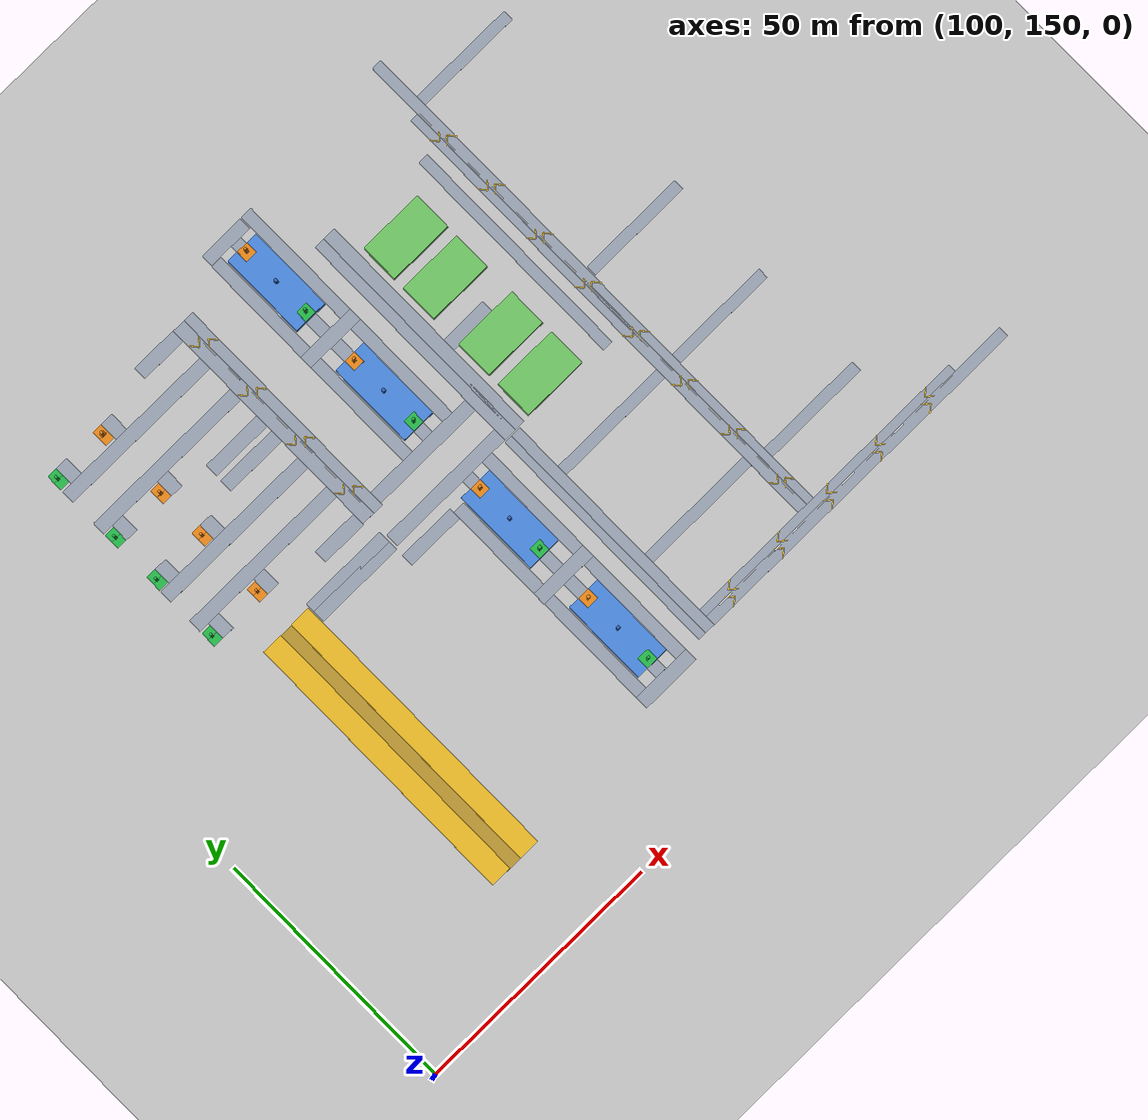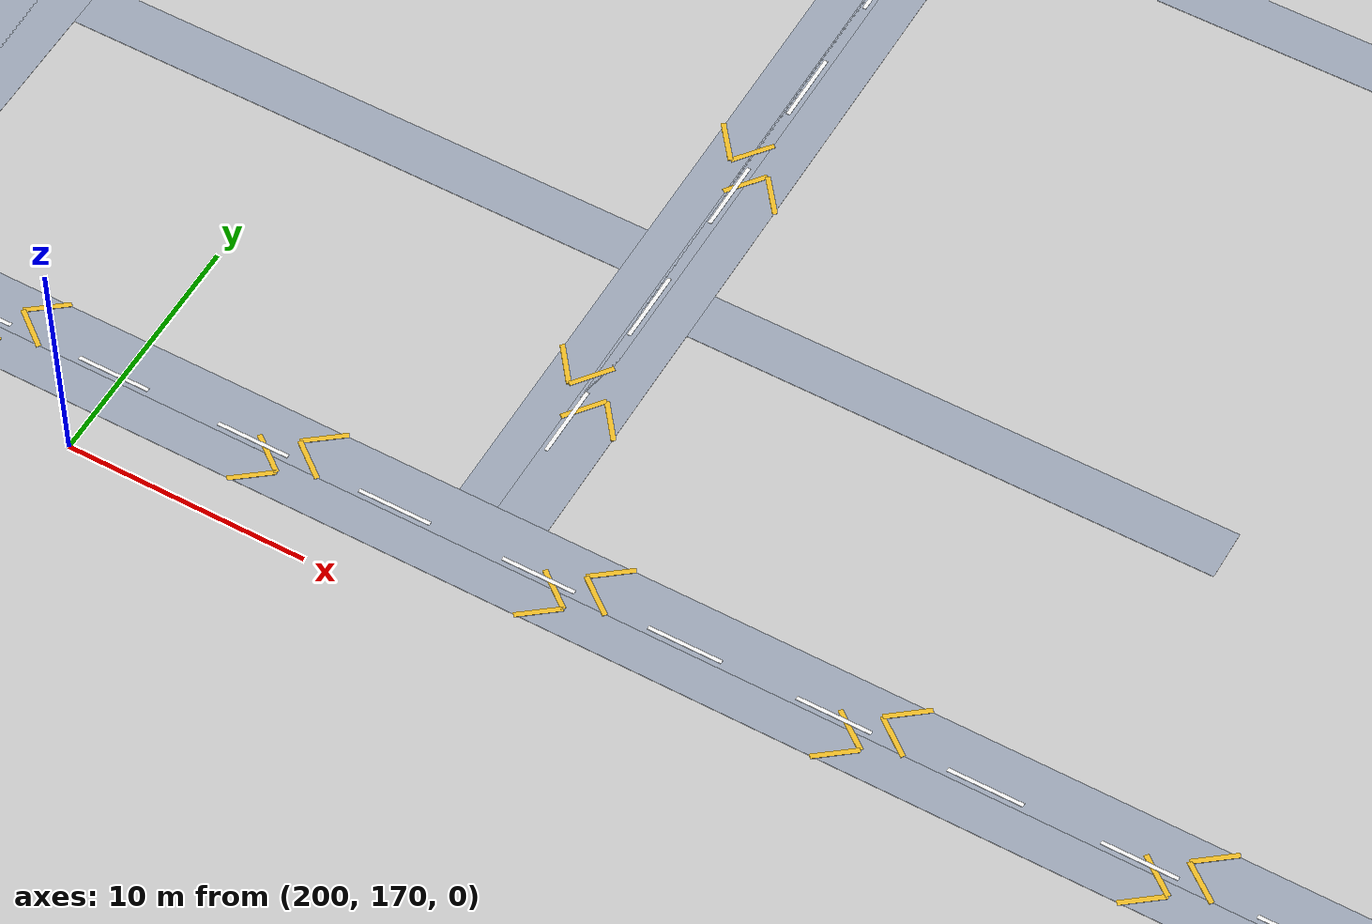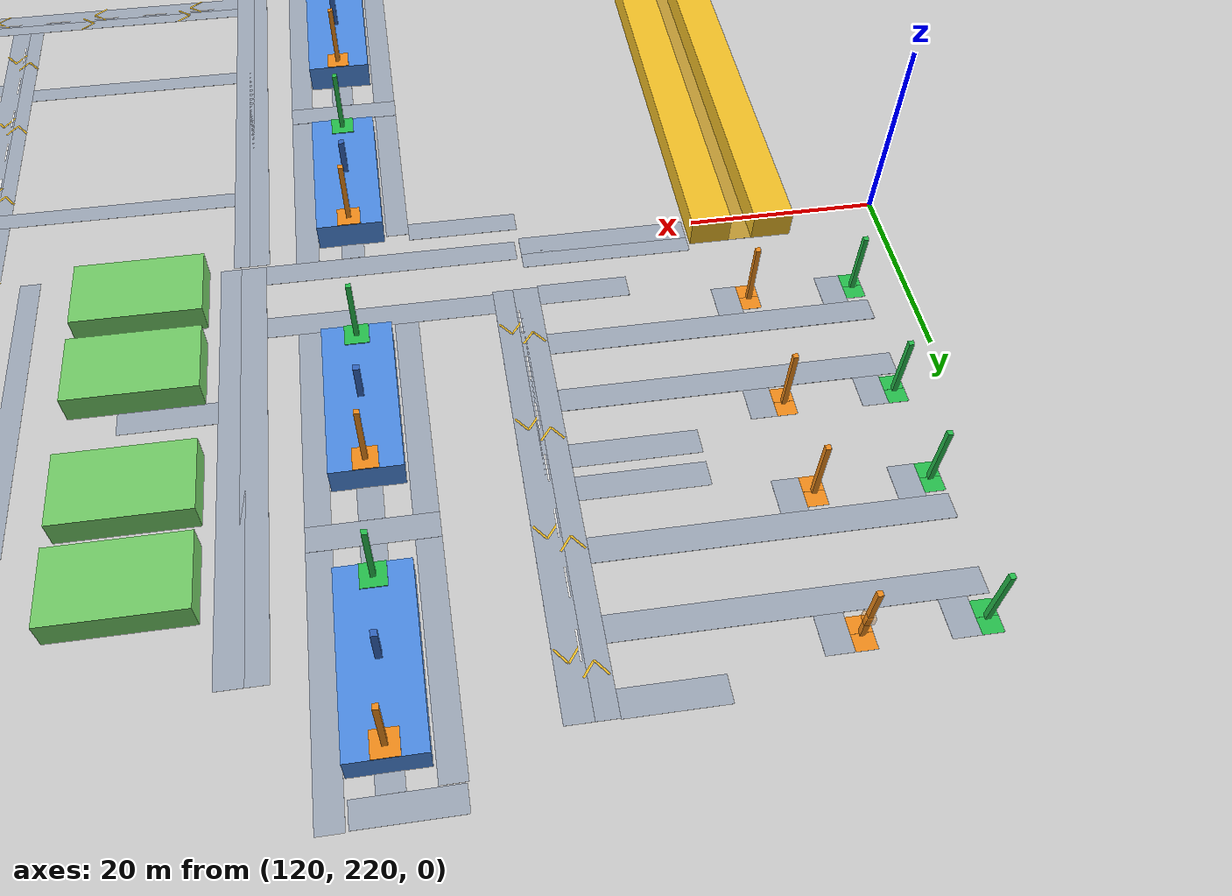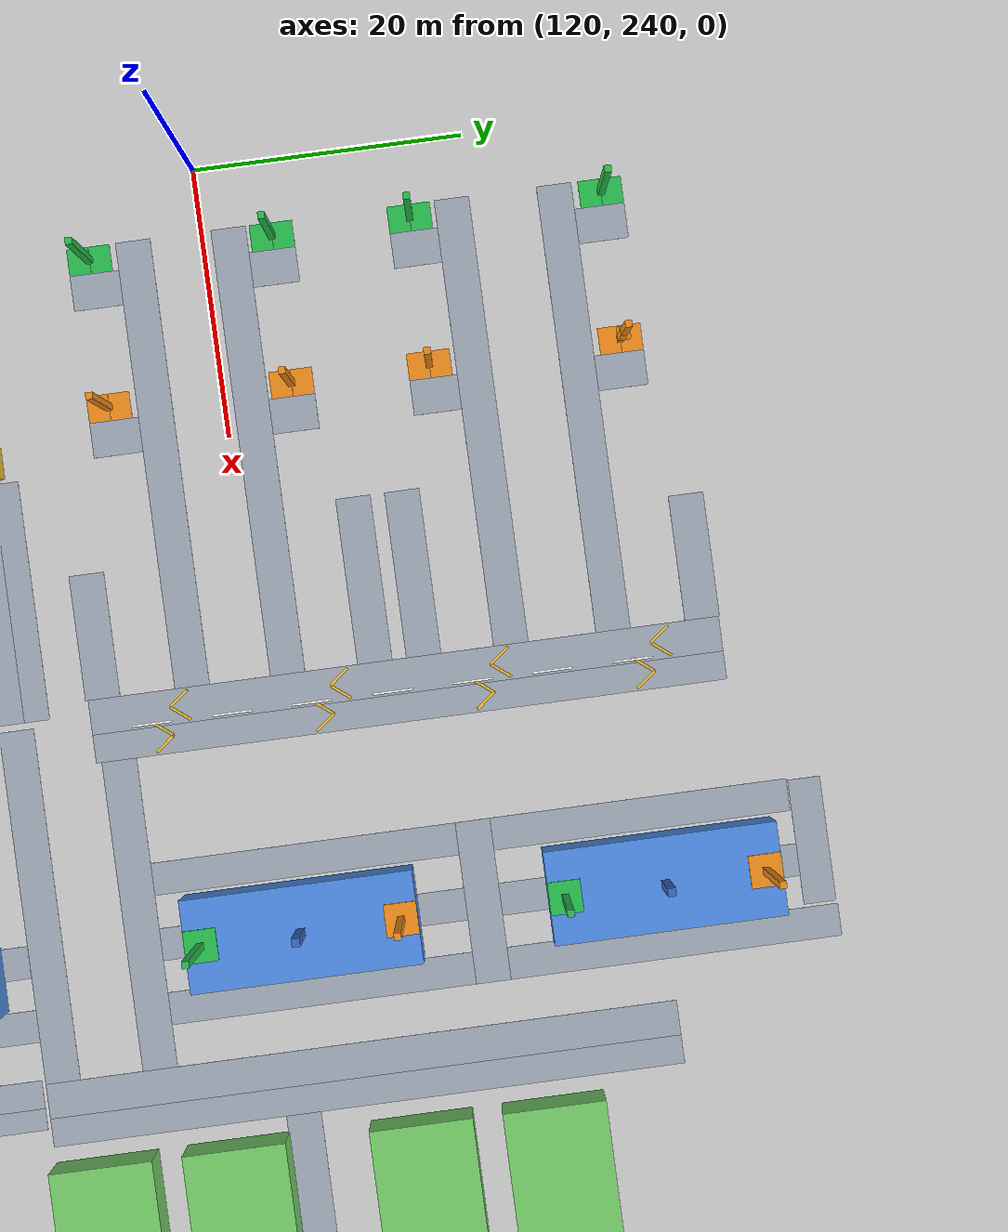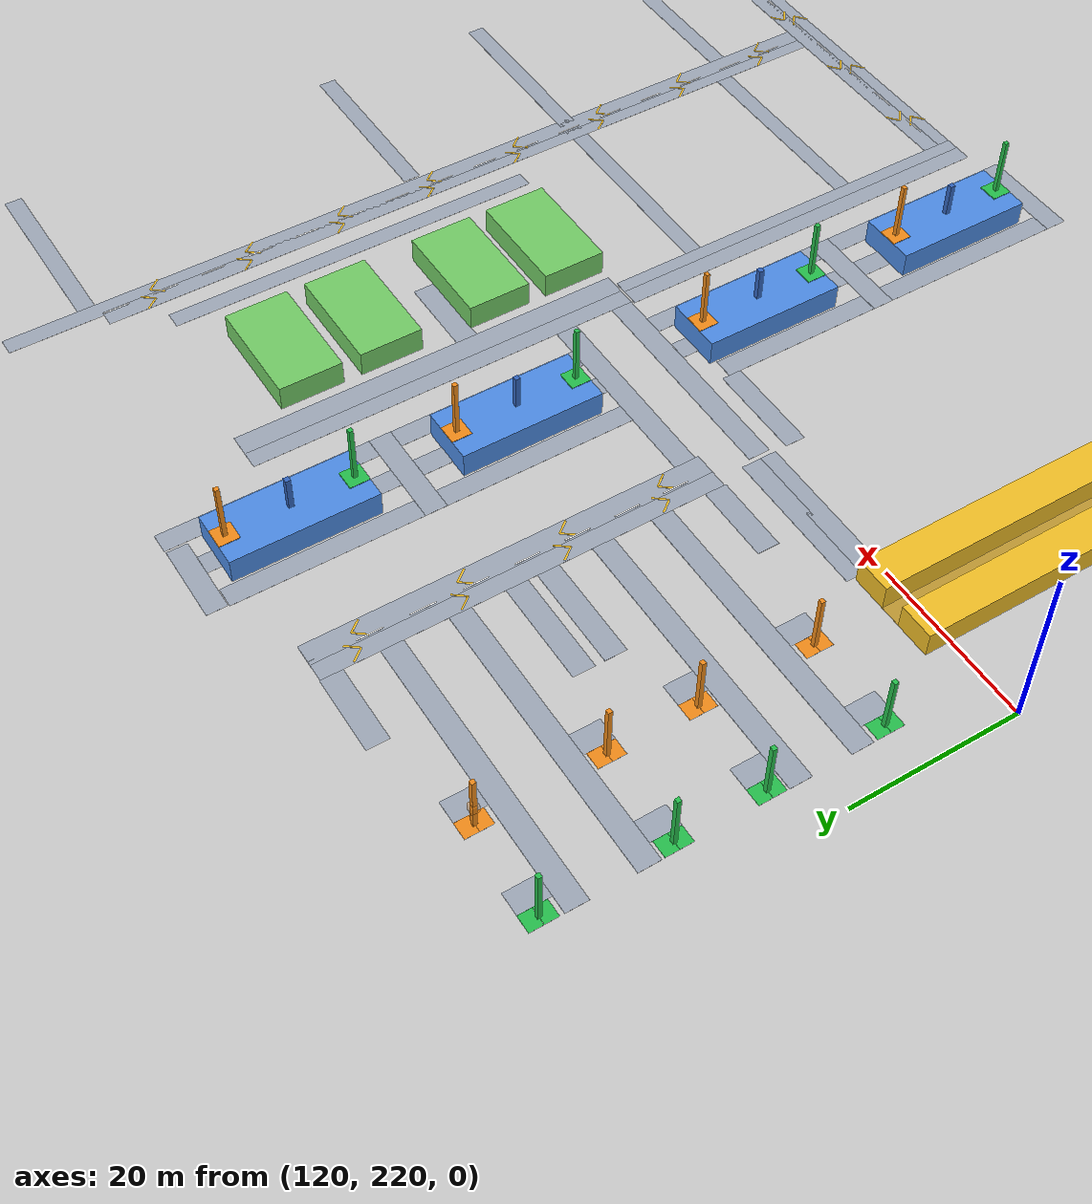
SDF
<?xml version="1.0"?>
<sdf version="1.6">
  <world name="cad_plant">
    <include><uri>model://sun</uri></include>
    <include><uri>model://ground_plane</uri></include>

    <physics type="ode">
      <max_step_size>0.001</max_step_size>
      <real_time_factor>1.0</real_time_factor>
      <real_time_update_rate>1000</real_time_update_rate>
      <ode>
        <solver><type>quick</type><iters>100</iters><sor>1.3</sor></solver>
        <constraints>
          <cfm>0.0</cfm><erp>0.2</erp>
          <contact_max_correcting_vel>100.0</contact_max_correcting_vel>
          <contact_surface_layer>0.001</contact_surface_layer>
        </constraints>
      </ode>
    </physics>

    <scene>
      <ambient>0.6 0.6 0.6 1</ambient>
      <background>0.75 0.80 0.86 1</background>
      <shadows>true</shadows>
    </scene>

    <gui>
      <!-- Over the cathode cell, not the origin. The origin is bare floor 200 m
           from the nearest machine. -->
      <camera name="user_camera">
        <pose>94.4 160.8 95.0 0 0.95 1.05</pose>
      </camera>
    </gui>

    <plugin name="gazebo_ros_state" filename="libgazebo_ros_state.so">
      <ros>
        <namespace>/gazebo</namespace>
      </ros>
      <update_rate>30.0</update_rate>
    </plugin>

    <model name="m_ASRS_rack_w">
      <static>true</static>
      <pose>132.058 194.720 1.500 0 0 0.0000</pose>
      <link name="link">
        <collision name="c"><geometry><box><size>4.215 56.740 3.000</size></box></geometry></collision>
        <visual name="v">
          <geometry><box><size>4.215 56.740 3.000</size></box></geometry>
          <material>
            <ambient>0.95 0.75 0.15 1</ambient>
            <diffuse>0.95 0.75 0.15 1</diffuse>
          </material>
        </visual>
      </link>
    </model>
    <model name="m_ASRS_rack_e">
      <static>true</static>
      <pose>138.772 194.720 1.500 0 0 0.0000</pose>
      <link name="link">
        <collision name="c"><geometry><box><size>4.215 56.740 3.000</size></box></geometry></collision>
        <visual name="v">
          <geometry><box><size>4.215 56.740 3.000</size></box></geometry>
          <material>
            <ambient>0.95 0.75 0.15 1</ambient>
            <diffuse>0.95 0.75 0.15 1</diffuse>
          </material>
        </visual>
      </link>
    </model>
    <model name="ASRS_crane_aisle">
      <static>true</static>
      <pose>135.415 194.720 0.020 0 0 0.0000</pose>
      <link name="link">
        <visual name="v">
          <geometry><box><size>2.500 56.740 0.020</size></box></geometry>
          <material>
            <ambient>0.75 0.6 0.2 1</ambient>
            <diffuse>0.75 0.6 0.2 1</diffuse>
          </material>
        </visual>
      </link>
    </model>
    <model name="m_GRV1">
      <static>true</static>
      <pose>176.630 182.900 1.500 0 0 0.0000</pose>
      <link name="link">
        <collision name="c"><geometry><box><size>6.880 17.100 3.000</size></box></geometry></collision>
        <visual name="v">
          <geometry><box><size>6.880 17.100 3.000</size></box></geometry>
          <material>
            <ambient>0.3 0.55 0.9 1</ambient>
            <diffuse>0.3 0.55 0.9 1</diffuse>
          </material>
        </visual>
      </link>
    </model>
    <model name="m_GRV2">
      <static>true</static>
      <pose>176.630 209.610 1.500 0 0 0.0000</pose>
      <link name="link">
        <collision name="c"><geometry><box><size>6.880 17.100 3.000</size></box></geometry></collision>
        <visual name="v">
          <geometry><box><size>6.880 17.100 3.000</size></box></geometry>
          <material>
            <ambient>0.3 0.55 0.9 1</ambient>
            <diffuse>0.3 0.55 0.9 1</diffuse>
          </material>
        </visual>
      </link>
    </model>
    <model name="m_GRV3">
      <static>true</static>
      <pose>176.630 240.770 1.500 0 0 0.0000</pose>
      <link name="link">
        <collision name="c"><geometry><box><size>6.880 17.100 3.000</size></box></geometry></collision>
        <visual name="v">
          <geometry><box><size>6.880 17.100 3.000</size></box></geometry>
          <material>
            <ambient>0.3 0.55 0.9 1</ambient>
            <diffuse>0.3 0.55 0.9 1</diffuse>
          </material>
        </visual>
      </link>
    </model>
    <model name="m_GRV4">
      <static>true</static>
      <pose>176.630 267.480 1.500 0 0 0.0000</pose>
      <link name="link">
        <collision name="c"><geometry><box><size>6.880 17.100 3.000</size></box></geometry></collision>
        <visual name="v">
          <geometry><box><size>6.880 17.100 3.000</size></box></geometry>
          <material>
            <ambient>0.3 0.55 0.9 1</ambient>
            <diffuse>0.3 0.55 0.9 1</diffuse>
          </material>
        </visual>
      </link>
    </model>
    <model name="m_SLT1">
      <static>true</static>
      <pose>198.165 224.030 1.500 0 0 0.0000</pose>
      <link name="link">
        <collision name="c"><geometry><box><size>13.050 7.600 3.000</size></box></geometry></collision>
        <visual name="v">
          <geometry><box><size>13.050 7.600 3.000</size></box></geometry>
          <material>
            <ambient>0.45 0.8 0.4 1</ambient>
            <diffuse>0.45 0.8 0.4 1</diffuse>
          </material>
        </visual>
      </link>
    </model>
    <model name="m_SLT2">
      <static>true</static>
      <pose>198.165 233.810 1.500 0 0 0.0000</pose>
      <link name="link">
        <collision name="c"><geometry><box><size>13.050 7.600 3.000</size></box></geometry></collision>
        <visual name="v">
          <geometry><box><size>13.050 7.600 3.000</size></box></geometry>
          <material>
            <ambient>0.45 0.8 0.4 1</ambient>
            <diffuse>0.45 0.8 0.4 1</diffuse>
          </material>
        </visual>
      </link>
    </model>
    <model name="m_SLT3">
      <static>true</static>
      <pose>198.165 247.530 1.500 0 0 0.0000</pose>
      <link name="link">
        <collision name="c"><geometry><box><size>13.050 7.600 3.000</size></box></geometry></collision>
        <visual name="v">
          <geometry><box><size>13.050 7.600 3.000</size></box></geometry>
          <material>
            <ambient>0.45 0.8 0.4 1</ambient>
            <diffuse>0.45 0.8 0.4 1</diffuse>
          </material>
        </visual>
      </link>
    </model>
    <model name="m_SLT4">
      <static>true</static>
      <pose>198.165 257.310 1.500 0 0 0.0000</pose>
      <link name="link">
        <collision name="c"><geometry><box><size>13.050 7.600 3.000</size></box></geometry></collision>
        <visual name="v">
          <geometry><box><size>13.050 7.600 3.000</size></box></geometry>
          <material>
            <ambient>0.45 0.8 0.4 1</ambient>
            <diffuse>0.45 0.8 0.4 1</diffuse>
          </material>
        </visual>
      </link>
    </model>
    <model name="lane_01">
      <static>true</static>
      <pose>141.250 234.830 0.020 0 0 0.0000</pose>
      <link name="link">
        <visual name="v">
          <geometry><box><size>33.380 2.600 0.020</size></box></geometry>
          <material>
            <ambient>0.62 0.66 0.72 1</ambient>
            <diffuse>0.62 0.66 0.72 1</diffuse>
          </material>
        </visual>
      </link>
    </model>
    <model name="lane_02">
      <static>true</static>
      <pose>141.250 241.980 0.020 0 0 0.0000</pose>
      <link name="link">
        <visual name="v">
          <geometry><box><size>33.380 2.600 0.020</size></box></geometry>
          <material>
            <ambient>0.62 0.66 0.72 1</ambient>
            <diffuse>0.62 0.66 0.72 1</diffuse>
          </material>
        </visual>
      </link>
    </model>
    <model name="lane_03">
      <static>true</static>
      <pose>141.250 258.700 0.020 0 0 0.0000</pose>
      <link name="link">
        <visual name="v">
          <geometry><box><size>33.380 2.600 0.020</size></box></geometry>
          <material>
            <ambient>0.62 0.66 0.72 1</ambient>
            <diffuse>0.62 0.66 0.72 1</diffuse>
          </material>
        </visual>
      </link>
    </model>
    <model name="lane_04">
      <static>true</static>
      <pose>141.250 266.360 0.020 0 0 0.0000</pose>
      <link name="link">
        <visual name="v">
          <geometry><box><size>33.380 2.600 0.020</size></box></geometry>
          <material>
            <ambient>0.62 0.66 0.72 1</ambient>
            <diffuse>0.62 0.66 0.72 1</diffuse>
          </material>
        </visual>
      </link>
    </model>
    <model name="lane_05">
      <static>true</static>
      <pose>150.050 220.920 0.020 0 0 0.0000</pose>
      <link name="link">
        <visual name="v">
          <geometry><box><size>17.840 2.400 0.020</size></box></geometry>
          <material>
            <ambient>0.62 0.66 0.72 1</ambient>
            <diffuse>0.62 0.66 0.72 1</diffuse>
          </material>
        </visual>
      </link>
    </model>
    <model name="lane_06">
      <static>true</static>
      <pose>150.050 222.820 0.020 0 0 0.0000</pose>
      <link name="link">
        <visual name="v">
          <geometry><box><size>17.840 2.400 0.020</size></box></geometry>
          <material>
            <ambient>0.62 0.66 0.72 1</ambient>
            <diffuse>0.62 0.66 0.72 1</diffuse>
          </material>
        </visual>
      </link>
    </model>
    <model name="lane_07">
      <static>true</static>
      <pose>151.755 248.510 0.020 0 0 0.0000</pose>
      <link name="link">
        <visual name="v">
          <geometry><box><size>12.370 2.600 0.020</size></box></geometry>
          <material>
            <ambient>0.62 0.66 0.72 1</ambient>
            <diffuse>0.62 0.66 0.72 1</diffuse>
          </material>
        </visual>
      </link>
    </model>
    <model name="lane_08">
      <static>true</static>
      <pose>151.755 252.170 0.020 0 0 0.0000</pose>
      <link name="link">
        <visual name="v">
          <geometry><box><size>12.370 2.600 0.020</size></box></geometry>
          <material>
            <ambient>0.62 0.66 0.72 1</ambient>
            <diffuse>0.62 0.66 0.72 1</diffuse>
          </material>
        </visual>
      </link>
    </model>
    <model name="lane_09">
      <static>true</static>
      <pose>153.285 228.130 0.020 0 0 0.0000</pose>
      <link name="link">
        <visual name="v">
          <geometry><box><size>9.310 2.600 0.020</size></box></geometry>
          <material>
            <ambient>0.62 0.66 0.72 1</ambient>
            <diffuse>0.62 0.66 0.72 1</diffuse>
          </material>
        </visual>
      </link>
    </model>
    <model name="lane_10">
      <static>true</static>
      <pose>153.285 273.030 0.020 0 0 0.0000</pose>
      <link name="link">
        <visual name="v">
          <geometry><box><size>9.310 2.600 0.020</size></box></geometry>
          <material>
            <ambient>0.62 0.66 0.72 1</ambient>
            <diffuse>0.62 0.66 0.72 1</diffuse>
          </material>
        </visual>
      </link>
    </model>
    <model name="lane_11">
      <static>true</static>
      <pose>164.775 217.120 0.020 0 0 0.0000</pose>
      <link name="link">
        <visual name="v">
          <geometry><box><size>11.610 2.400 0.020</size></box></geometry>
          <material>
            <ambient>0.62 0.66 0.72 1</ambient>
            <diffuse>0.62 0.66 0.72 1</diffuse>
          </material>
        </visual>
      </link>
    </model>
    <model name="lane_12">
      <static>true</static>
      <pose>172.630 221.440 0.020 0 0 0.0000</pose>
      <link name="link">
        <visual name="v">
          <geometry><box><size>26.300 2.600 0.020</size></box></geometry>
          <material>
            <ambient>0.62 0.66 0.72 1</ambient>
            <diffuse>0.62 0.66 0.72 1</diffuse>
          </material>
        </visual>
      </link>
    </model>
    <model name="lane_13">
      <static>true</static>
      <pose>174.210 228.720 0.020 0 0 0.0000</pose>
      <link name="link">
        <visual name="v">
          <geometry><box><size>23.140 2.600 0.020</size></box></geometry>
          <material>
            <ambient>0.62 0.66 0.72 1</ambient>
            <diffuse>0.62 0.66 0.72 1</diffuse>
          </material>
        </visual>
      </link>
    </model>
    <model name="lane_14">
      <static>true</static>
      <pose>175.340 278.910 0.020 0 0 0.0000</pose>
      <link name="link">
        <visual name="v">
          <geometry><box><size>9.300 2.400 0.020</size></box></geometry>
          <material>
            <ambient>0.62 0.66 0.72 1</ambient>
            <diffuse>0.62 0.66 0.72 1</diffuse>
          </material>
        </visual>
      </link>
    </model>
    <model name="lane_15">
      <static>true</static>
      <pose>225.075 172.700 0.020 0 0 0.0000</pose>
      <link name="link">
        <visual name="v">
          <geometry><box><size>71.850 2.100 0.020</size></box></geometry>
          <material>
            <ambient>0.62 0.66 0.72 1</ambient>
            <diffuse>0.62 0.66 0.72 1</diffuse>
          </material>
        </visual>
      </link>
    </model>
    <model name="lane_16">
      <static>true</static>
      <pose>219.655 174.300 0.020 0 0 0.0000</pose>
      <link name="link">
        <visual name="v">
          <geometry><box><size>61.010 2.100 0.020</size></box></geometry>
          <material>
            <ambient>0.62 0.66 0.72 1</ambient>
            <diffuse>0.62 0.66 0.72 1</diffuse>
          </material>
        </visual>
      </link>
    </model>
    <model name="lane_17">
      <static>true</static>
      <pose>201.200 187.910 0.020 0 0 0.0000</pose>
      <link name="link">
        <visual name="v">
          <geometry><box><size>24.100 2.100 0.020</size></box></geometry>
          <material>
            <ambient>0.62 0.66 0.72 1</ambient>
            <diffuse>0.62 0.66 0.72 1</diffuse>
          </material>
        </visual>
      </link>
    </model>
    <model name="lane_18">
      <static>true</static>
      <pose>213.730 209.370 0.020 0 0 0.0000</pose>
      <link name="link">
        <visual name="v">
          <geometry><box><size>49.160 2.100 0.020</size></box></geometry>
          <material>
            <ambient>0.62 0.66 0.72 1</ambient>
            <diffuse>0.62 0.66 0.72 1</diffuse>
          </material>
        </visual>
      </link>
    </model>
    <model name="lane_19">
      <static>true</static>
      <pose>195.245 238.830 0.020 0 0 0.0000</pose>
      <link name="link">
        <visual name="v">
          <geometry><box><size>9.530 2.600 0.020</size></box></geometry>
          <material>
            <ambient>0.62 0.66 0.72 1</ambient>
            <diffuse>0.62 0.66 0.72 1</diffuse>
          </material>
        </visual>
      </link>
    </model>
    <model name="lane_20">
      <static>true</static>
      <pose>227.745 186.440 0.020 0 0 0.0000</pose>
      <link name="link">
        <visual name="v">
          <geometry><box><size>21.590 2.100 0.020</size></box></geometry>
          <material>
            <ambient>0.62 0.66 0.72 1</ambient>
            <diffuse>0.62 0.66 0.72 1</diffuse>
          </material>
        </visual>
      </link>
    </model>
    <model name="lane_21">
      <static>true</static>
      <pose>227.630 272.760 0.020 0 0 0.0000</pose>
      <link name="link">
        <visual name="v">
          <geometry><box><size>21.360 2.100 0.020</size></box></geometry>
          <material>
            <ambient>0.62 0.66 0.72 1</ambient>
            <diffuse>0.62 0.66 0.72 1</diffuse>
          </material>
        </visual>
      </link>
    </model>
    <model name="lane_22">
      <static>true</static>
      <pose>227.970 230.700 0.020 0 0 0.0000</pose>
      <link name="link">
        <visual name="v">
          <geometry><box><size>21.580 2.100 0.020</size></box></geometry>
          <material>
            <ambient>0.62 0.66 0.72 1</ambient>
            <diffuse>0.62 0.66 0.72 1</diffuse>
          </material>
        </visual>
      </link>
    </model>
    <model name="lane_23">
      <static>true</static>
      <pose>159.240 250.635 0.020 0 0 0.0000</pose>
      <link name="link">
        <visual name="v">
          <geometry><box><size>2.600 47.230 0.020</size></box></geometry>
          <material>
            <ambient>0.62 0.66 0.72 1</ambient>
            <diffuse>0.62 0.66 0.72 1</diffuse>
          </material>
        </visual>
      </link>
    </model>
    <model name="lane_24">
      <static>true</static>
      <pose>161.340 250.635 0.020 0 0 0.0000</pose>
      <link name="link">
        <visual name="v">
          <geometry><box><size>2.600 47.230 0.020</size></box></geometry>
          <material>
            <ambient>0.62 0.66 0.72 1</ambient>
            <diffuse>0.62 0.66 0.72 1</diffuse>
          </material>
        </visual>
      </link>
    </model>
    <model name="lane_25">
      <static>true</static>
      <pose>171.750 253.815 0.020 0 0 0.0000</pose>
      <link name="link">
        <visual name="v">
          <geometry><box><size>2.400 47.590 0.020</size></box></geometry>
          <material>
            <ambient>0.62 0.66 0.72 1</ambient>
            <diffuse>0.62 0.66 0.72 1</diffuse>
          </material>
        </visual>
      </link>
    </model>
    <model name="lane_26">
      <static>true</static>
      <pose>171.780 193.620 0.020 0 0 0.0000</pose>
      <link name="link">
        <visual name="v">
          <geometry><box><size>2.400 47.580 0.020</size></box></geometry>
          <material>
            <ambient>0.62 0.66 0.72 1</ambient>
            <diffuse>0.62 0.66 0.72 1</diffuse>
          </material>
        </visual>
      </link>
    </model>
    <model name="lane_27">
      <static>true</static>
      <pose>181.430 195.045 0.020 0 0 0.0000</pose>
      <link name="link">
        <visual name="v">
          <geometry><box><size>2.400 50.190 0.020</size></box></geometry>
          <material>
            <ambient>0.62 0.66 0.72 1</ambient>
            <diffuse>0.62 0.66 0.72 1</diffuse>
          </material>
        </visual>
      </link>
    </model>
    <model name="lane_28">
      <static>true</static>
      <pose>181.430 255.110 0.020 0 0 0.0000</pose>
      <link name="link">
        <visual name="v">
          <geometry><box><size>2.400 50.180 0.020</size></box></geometry>
          <material>
            <ambient>0.62 0.66 0.72 1</ambient>
            <diffuse>0.62 0.66 0.72 1</diffuse>
          </material>
        </visual>
      </link>
    </model>
    <model name="lane_29">
      <static>true</static>
      <pose>186.500 195.765 0.020 0 0 0.0000</pose>
      <link name="link">
        <visual name="v">
          <geometry><box><size>2.100 48.210 0.020</size></box></geometry>
          <material>
            <ambient>0.62 0.66 0.72 1</ambient>
            <diffuse>0.62 0.66 0.72 1</diffuse>
          </material>
        </visual>
      </link>
    </model>
    <model name="lane_30">
      <static>true</static>
      <pose>187.080 243.760 0.020 0 0 0.0000</pose>
      <link name="link">
        <visual name="v">
          <geometry><box><size>2.600 47.240 0.020</size></box></geometry>
          <material>
            <ambient>0.62 0.66 0.72 1</ambient>
            <diffuse>0.62 0.66 0.72 1</diffuse>
          </material>
        </visual>
      </link>
    </model>
    <model name="lane_31">
      <static>true</static>
      <pose>188.100 195.765 0.020 0 0 0.0000</pose>
      <link name="link">
        <visual name="v">
          <geometry><box><size>2.100 48.210 0.020</size></box></geometry>
          <material>
            <ambient>0.62 0.66 0.72 1</ambient>
            <diffuse>0.62 0.66 0.72 1</diffuse>
          </material>
        </visual>
      </link>
    </model>
    <model name="lane_32">
      <static>true</static>
      <pose>189.180 243.760 0.020 0 0 0.0000</pose>
      <link name="link">
        <visual name="v">
          <geometry><box><size>2.600 47.240 0.020</size></box></geometry>
          <material>
            <ambient>0.62 0.66 0.72 1</ambient>
            <diffuse>0.62 0.66 0.72 1</diffuse>
          </material>
        </visual>
      </link>
    </model>
    <model name="lane_33">
      <static>true</static>
      <pose>210.090 242.285 0.020 0 0 0.0000</pose>
      <link name="link">
        <visual name="v">
          <geometry><box><size>2.100 46.010 0.020</size></box></geometry>
          <material>
            <ambient>0.62 0.66 0.72 1</ambient>
            <diffuse>0.62 0.66 0.72 1</diffuse>
          </material>
        </visual>
      </link>
    </model>
    <model name="lane_34">
      <static>true</static>
      <pose>214.300 223.415 0.020 0 0 0.0000</pose>
      <link name="link">
        <visual name="v">
          <geometry><box><size>2.100 96.130 0.020</size></box></geometry>
          <material>
            <ambient>0.62 0.66 0.72 1</ambient>
            <diffuse>0.62 0.66 0.72 1</diffuse>
          </material>
        </visual>
      </link>
    </model>
    <model name="lane_35">
      <static>true</static>
      <pose>215.900 229.055 0.020 0 0 0.0000</pose>
      <link name="link">
        <visual name="v">
          <geometry><box><size>2.100 107.410 0.020</size></box></geometry>
          <material>
            <ambient>0.62 0.66 0.72 1</ambient>
            <diffuse>0.62 0.66 0.72 1</diffuse>
          </material>
        </visual>
      </link>
    </model>
    <model name="road1_div01">
      <static>true</static>
      <pose>160.290 231.520 0.080 0 0 0.0000</pose>
      <link name="link">
        <visual name="v">
          <geometry><box><size>0.160 3.000 0.020</size></box></geometry>
          <material>
            <ambient>0.97 0.97 0.97 1</ambient>
            <diffuse>0.97 0.97 0.97 1</diffuse>
          </material>
        </visual>
      </link>
    </model>
    <model name="road1_div02">
      <static>true</static>
      <pose>160.290 237.520 0.080 0 0 0.0000</pose>
      <link name="link">
        <visual name="v">
          <geometry><box><size>0.160 3.000 0.020</size></box></geometry>
          <material>
            <ambient>0.97 0.97 0.97 1</ambient>
            <diffuse>0.97 0.97 0.97 1</diffuse>
          </material>
        </visual>
      </link>
    </model>
    <model name="road1_div03">
      <static>true</static>
      <pose>160.290 243.520 0.080 0 0 0.0000</pose>
      <link name="link">
        <visual name="v">
          <geometry><box><size>0.160 3.000 0.020</size></box></geometry>
          <material>
            <ambient>0.97 0.97 0.97 1</ambient>
            <diffuse>0.97 0.97 0.97 1</diffuse>
          </material>
        </visual>
      </link>
    </model>
    <model name="road1_div04">
      <static>true</static>
      <pose>160.290 249.520 0.080 0 0 0.0000</pose>
      <link name="link">
        <visual name="v">
          <geometry><box><size>0.160 3.000 0.020</size></box></geometry>
          <material>
            <ambient>0.97 0.97 0.97 1</ambient>
            <diffuse>0.97 0.97 0.97 1</diffuse>
          </material>
        </visual>
      </link>
    </model>
    <model name="road1_div05">
      <static>true</static>
      <pose>160.290 255.520 0.080 0 0 0.0000</pose>
      <link name="link">
        <visual name="v">
          <geometry><box><size>0.160 3.000 0.020</size></box></geometry>
          <material>
            <ambient>0.97 0.97 0.97 1</ambient>
            <diffuse>0.97 0.97 0.97 1</diffuse>
          </material>
        </visual>
      </link>
    </model>
    <model name="road1_div06">
      <static>true</static>
      <pose>160.290 261.520 0.080 0 0 0.0000</pose>
      <link name="link">
        <visual name="v">
          <geometry><box><size>0.160 3.000 0.020</size></box></geometry>
          <material>
            <ambient>0.97 0.97 0.97 1</ambient>
            <diffuse>0.97 0.97 0.97 1</diffuse>
          </material>
        </visual>
      </link>
    </model>
    <model name="road1_div07">
      <static>true</static>
      <pose>160.290 267.520 0.080 0 0 0.0000</pose>
      <link name="link">
        <visual name="v">
          <geometry><box><size>0.160 3.000 0.020</size></box></geometry>
          <material>
            <ambient>0.97 0.97 0.97 1</ambient>
            <diffuse>0.97 0.97 0.97 1</diffuse>
          </material>
        </visual>
      </link>
    </model>
    <model name="road1a_arw01l">
      <static>true</static>
      <pose>158.686 233.729 0.070 0 0 8.5172</pose>
      <link name="link">
        <visual name="v">
          <geometry><box><size>1.800 0.200 0.020</size></box></geometry>
          <material>
            <ambient>0.95 0.75 0.15 1</ambient>
            <diffuse>0.95 0.75 0.15 1</diffuse>
          </material>
        </visual>
      </link>
    </model>
    <model name="road1a_arw01r">
      <static>true</static>
      <pose>159.794 233.729 0.070 0 0 7.1908</pose>
      <link name="link">
        <visual name="v">
          <geometry><box><size>1.800 0.200 0.020</size></box></geometry>
          <material>
            <ambient>0.95 0.75 0.15 1</ambient>
            <diffuse>0.95 0.75 0.15 1</diffuse>
          </material>
        </visual>
      </link>
    </model>
    <model name="road1a_arw02l">
      <static>true</static>
      <pose>158.686 245.729 0.070 0 0 8.5172</pose>
      <link name="link">
        <visual name="v">
          <geometry><box><size>1.800 0.200 0.020</size></box></geometry>
          <material>
            <ambient>0.95 0.75 0.15 1</ambient>
            <diffuse>0.95 0.75 0.15 1</diffuse>
          </material>
        </visual>
      </link>
    </model>
    <model name="road1a_arw02r">
      <static>true</static>
      <pose>159.794 245.729 0.070 0 0 7.1908</pose>
      <link name="link">
        <visual name="v">
          <geometry><box><size>1.800 0.200 0.020</size></box></geometry>
          <material>
            <ambient>0.95 0.75 0.15 1</ambient>
            <diffuse>0.95 0.75 0.15 1</diffuse>
          </material>
        </visual>
      </link>
    </model>
    <model name="road1a_arw03l">
      <static>true</static>
      <pose>158.686 257.729 0.070 0 0 8.5172</pose>
      <link name="link">
        <visual name="v">
          <geometry><box><size>1.800 0.200 0.020</size></box></geometry>
          <material>
            <ambient>0.95 0.75 0.15 1</ambient>
            <diffuse>0.95 0.75 0.15 1</diffuse>
          </material>
        </visual>
      </link>
    </model>
    <model name="road1a_arw03r">
      <static>true</static>
      <pose>159.794 257.729 0.070 0 0 7.1908</pose>
      <link name="link">
        <visual name="v">
          <geometry><box><size>1.800 0.200 0.020</size></box></geometry>
          <material>
            <ambient>0.95 0.75 0.15 1</ambient>
            <diffuse>0.95 0.75 0.15 1</diffuse>
          </material>
        </visual>
      </link>
    </model>
    <model name="road1a_arw04l">
      <static>true</static>
      <pose>158.686 269.729 0.070 0 0 8.5172</pose>
      <link name="link">
        <visual name="v">
          <geometry><box><size>1.800 0.200 0.020</size></box></geometry>
          <material>
            <ambient>0.95 0.75 0.15 1</ambient>
            <diffuse>0.95 0.75 0.15 1</diffuse>
          </material>
        </visual>
      </link>
    </model>
    <model name="road1a_arw04r">
      <static>true</static>
      <pose>159.794 269.729 0.070 0 0 7.1908</pose>
      <link name="link">
        <visual name="v">
          <geometry><box><size>1.800 0.200 0.020</size></box></geometry>
          <material>
            <ambient>0.95 0.75 0.15 1</ambient>
            <diffuse>0.95 0.75 0.15 1</diffuse>
          </material>
        </visual>
      </link>
    </model>
    <model name="road1b_arw01l">
      <static>true</static>
      <pose>161.894 232.311 0.070 0 0 5.3756</pose>
      <link name="link">
        <visual name="v">
          <geometry><box><size>1.800 0.200 0.020</size></box></geometry>
          <material>
            <ambient>0.95 0.75 0.15 1</ambient>
            <diffuse>0.95 0.75 0.15 1</diffuse>
          </material>
        </visual>
      </link>
    </model>
    <model name="road1b_arw01r">
      <static>true</static>
      <pose>160.786 232.311 0.070 0 0 4.0492</pose>
      <link name="link">
        <visual name="v">
          <geometry><box><size>1.800 0.200 0.020</size></box></geometry>
          <material>
            <ambient>0.95 0.75 0.15 1</ambient>
            <diffuse>0.95 0.75 0.15 1</diffuse>
          </material>
        </visual>
      </link>
    </model>
    <model name="road1b_arw02l">
      <static>true</static>
      <pose>161.894 244.311 0.070 0 0 5.3756</pose>
      <link name="link">
        <visual name="v">
          <geometry><box><size>1.800 0.200 0.020</size></box></geometry>
          <material>
            <ambient>0.95 0.75 0.15 1</ambient>
            <diffuse>0.95 0.75 0.15 1</diffuse>
          </material>
        </visual>
      </link>
    </model>
    <model name="road1b_arw02r">
      <static>true</static>
      <pose>160.786 244.311 0.070 0 0 4.0492</pose>
      <link name="link">
        <visual name="v">
          <geometry><box><size>1.800 0.200 0.020</size></box></geometry>
          <material>
            <ambient>0.95 0.75 0.15 1</ambient>
            <diffuse>0.95 0.75 0.15 1</diffuse>
          </material>
        </visual>
      </link>
    </model>
    <model name="road1b_arw03l">
      <static>true</static>
      <pose>161.894 256.311 0.070 0 0 5.3756</pose>
      <link name="link">
        <visual name="v">
          <geometry><box><size>1.800 0.200 0.020</size></box></geometry>
          <material>
            <ambient>0.95 0.75 0.15 1</ambient>
            <diffuse>0.95 0.75 0.15 1</diffuse>
          </material>
        </visual>
      </link>
    </model>
    <model name="road1b_arw03r">
      <static>true</static>
      <pose>160.786 256.311 0.070 0 0 4.0492</pose>
      <link name="link">
        <visual name="v">
          <geometry><box><size>1.800 0.200 0.020</size></box></geometry>
          <material>
            <ambient>0.95 0.75 0.15 1</ambient>
            <diffuse>0.95 0.75 0.15 1</diffuse>
          </material>
        </visual>
      </link>
    </model>
    <model name="road1b_arw04l">
      <static>true</static>
      <pose>161.894 268.311 0.070 0 0 5.3756</pose>
      <link name="link">
        <visual name="v">
          <geometry><box><size>1.800 0.200 0.020</size></box></geometry>
          <material>
            <ambient>0.95 0.75 0.15 1</ambient>
            <diffuse>0.95 0.75 0.15 1</diffuse>
          </material>
        </visual>
      </link>
    </model>
    <model name="road1b_arw04r">
      <static>true</static>
      <pose>160.786 268.311 0.070 0 0 4.0492</pose>
      <link name="link">
        <visual name="v">
          <geometry><box><size>1.800 0.200 0.020</size></box></geometry>
          <material>
            <ambient>0.95 0.75 0.15 1</ambient>
            <diffuse>0.95 0.75 0.15 1</diffuse>
          </material>
        </visual>
      </link>
    </model>
    <model name="road2_div01">
      <static>true</static>
      <pose>215.100 179.850 0.080 0 0 0.0000</pose>
      <link name="link">
        <visual name="v">
          <geometry><box><size>0.160 3.000 0.020</size></box></geometry>
          <material>
            <ambient>0.97 0.97 0.97 1</ambient>
            <diffuse>0.97 0.97 0.97 1</diffuse>
          </material>
        </visual>
      </link>
    </model>
    <model name="road2_div02">
      <static>true</static>
      <pose>215.100 185.850 0.080 0 0 0.0000</pose>
      <link name="link">
        <visual name="v">
          <geometry><box><size>0.160 3.000 0.020</size></box></geometry>
          <material>
            <ambient>0.97 0.97 0.97 1</ambient>
            <diffuse>0.97 0.97 0.97 1</diffuse>
          </material>
        </visual>
      </link>
    </model>
    <model name="road2_div03">
      <static>true</static>
      <pose>215.100 191.850 0.080 0 0 0.0000</pose>
      <link name="link">
        <visual name="v">
          <geometry><box><size>0.160 3.000 0.020</size></box></geometry>
          <material>
            <ambient>0.97 0.97 0.97 1</ambient>
            <diffuse>0.97 0.97 0.97 1</diffuse>
          </material>
        </visual>
      </link>
    </model>
    <model name="road2_div04">
      <static>true</static>
      <pose>215.100 197.850 0.080 0 0 0.0000</pose>
      <link name="link">
        <visual name="v">
          <geometry><box><size>0.160 3.000 0.020</size></box></geometry>
          <material>
            <ambient>0.97 0.97 0.97 1</ambient>
            <diffuse>0.97 0.97 0.97 1</diffuse>
          </material>
        </visual>
      </link>
    </model>
    <model name="road2_div05">
      <static>true</static>
      <pose>215.100 203.850 0.080 0 0 0.0000</pose>
      <link name="link">
        <visual name="v">
          <geometry><box><size>0.160 3.000 0.020</size></box></geometry>
          <material>
            <ambient>0.97 0.97 0.97 1</ambient>
            <diffuse>0.97 0.97 0.97 1</diffuse>
          </material>
        </visual>
      </link>
    </model>
    <model name="road2_div06">
      <static>true</static>
      <pose>215.100 209.850 0.080 0 0 0.0000</pose>
      <link name="link">
        <visual name="v">
          <geometry><box><size>0.160 3.000 0.020</size></box></geometry>
          <material>
            <ambient>0.97 0.97 0.97 1</ambient>
            <diffuse>0.97 0.97 0.97 1</diffuse>
          </material>
        </visual>
      </link>
    </model>
    <model name="road2_div07">
      <static>true</static>
      <pose>215.100 215.850 0.080 0 0 0.0000</pose>
      <link name="link">
        <visual name="v">
          <geometry><box><size>0.160 3.000 0.020</size></box></geometry>
          <material>
            <ambient>0.97 0.97 0.97 1</ambient>
            <diffuse>0.97 0.97 0.97 1</diffuse>
          </material>
        </visual>
      </link>
    </model>
    <model name="road2_div08">
      <static>true</static>
      <pose>215.100 221.850 0.080 0 0 0.0000</pose>
      <link name="link">
        <visual name="v">
          <geometry><box><size>0.160 3.000 0.020</size></box></geometry>
          <material>
            <ambient>0.97 0.97 0.97 1</ambient>
            <diffuse>0.97 0.97 0.97 1</diffuse>
          </material>
        </visual>
      </link>
    </model>
    <model name="road2_div09">
      <static>true</static>
      <pose>215.100 227.850 0.080 0 0 0.0000</pose>
      <link name="link">
        <visual name="v">
          <geometry><box><size>0.160 3.000 0.020</size></box></geometry>
          <material>
            <ambient>0.97 0.97 0.97 1</ambient>
            <diffuse>0.97 0.97 0.97 1</diffuse>
          </material>
        </visual>
      </link>
    </model>
    <model name="road2_div10">
      <static>true</static>
      <pose>215.100 233.850 0.080 0 0 0.0000</pose>
      <link name="link">
        <visual name="v">
          <geometry><box><size>0.160 3.000 0.020</size></box></geometry>
          <material>
            <ambient>0.97 0.97 0.97 1</ambient>
            <diffuse>0.97 0.97 0.97 1</diffuse>
          </material>
        </visual>
      </link>
    </model>
    <model name="road2_div11">
      <static>true</static>
      <pose>215.100 239.850 0.080 0 0 0.0000</pose>
      <link name="link">
        <visual name="v">
          <geometry><box><size>0.160 3.000 0.020</size></box></geometry>
          <material>
            <ambient>0.97 0.97 0.97 1</ambient>
            <diffuse>0.97 0.97 0.97 1</diffuse>
          </material>
        </visual>
      </link>
    </model>
    <model name="road2_div12">
      <static>true</static>
      <pose>215.100 245.850 0.080 0 0 0.0000</pose>
      <link name="link">
        <visual name="v">
          <geometry><box><size>0.160 3.000 0.020</size></box></geometry>
          <material>
            <ambient>0.97 0.97 0.97 1</ambient>
            <diffuse>0.97 0.97 0.97 1</diffuse>
          </material>
        </visual>
      </link>
    </model>
    <model name="road2_div13">
      <static>true</static>
      <pose>215.100 251.850 0.080 0 0 0.0000</pose>
      <link name="link">
        <visual name="v">
          <geometry><box><size>0.160 3.000 0.020</size></box></geometry>
          <material>
            <ambient>0.97 0.97 0.97 1</ambient>
            <diffuse>0.97 0.97 0.97 1</diffuse>
          </material>
        </visual>
      </link>
    </model>
    <model name="road2_div14">
      <static>true</static>
      <pose>215.100 257.850 0.080 0 0 0.0000</pose>
      <link name="link">
        <visual name="v">
          <geometry><box><size>0.160 3.000 0.020</size></box></geometry>
          <material>
            <ambient>0.97 0.97 0.97 1</ambient>
            <diffuse>0.97 0.97 0.97 1</diffuse>
          </material>
        </visual>
      </link>
    </model>
    <model name="road2_div15">
      <static>true</static>
      <pose>215.100 263.850 0.080 0 0 0.0000</pose>
      <link name="link">
        <visual name="v">
          <geometry><box><size>0.160 3.000 0.020</size></box></geometry>
          <material>
            <ambient>0.97 0.97 0.97 1</ambient>
            <diffuse>0.97 0.97 0.97 1</diffuse>
          </material>
        </visual>
      </link>
    </model>
    <model name="road2_div16">
      <static>true</static>
      <pose>215.100 269.850 0.080 0 0 0.0000</pose>
      <link name="link">
        <visual name="v">
          <geometry><box><size>0.160 3.000 0.020</size></box></geometry>
          <material>
            <ambient>0.97 0.97 0.97 1</ambient>
            <diffuse>0.97 0.97 0.97 1</diffuse>
          </material>
        </visual>
      </link>
    </model>
    <model name="road2a_arw01l">
      <static>true</static>
      <pose>213.746 182.059 0.070 0 0 8.5172</pose>
      <link name="link">
        <visual name="v">
          <geometry><box><size>1.800 0.200 0.020</size></box></geometry>
          <material>
            <ambient>0.95 0.75 0.15 1</ambient>
            <diffuse>0.95 0.75 0.15 1</diffuse>
          </material>
        </visual>
      </link>
    </model>
    <model name="road2a_arw01r">
      <static>true</static>
      <pose>214.854 182.059 0.070 0 0 7.1908</pose>
      <link name="link">
        <visual name="v">
          <geometry><box><size>1.800 0.200 0.020</size></box></geometry>
          <material>
            <ambient>0.95 0.75 0.15 1</ambient>
            <diffuse>0.95 0.75 0.15 1</diffuse>
          </material>
        </visual>
      </link>
    </model>
    <model name="road2a_arw02l">
      <static>true</static>
      <pose>213.746 194.059 0.070 0 0 8.5172</pose>
      <link name="link">
        <visual name="v">
          <geometry><box><size>1.800 0.200 0.020</size></box></geometry>
          <material>
            <ambient>0.95 0.75 0.15 1</ambient>
            <diffuse>0.95 0.75 0.15 1</diffuse>
          </material>
        </visual>
      </link>
    </model>
    <model name="road2a_arw02r">
      <static>true</static>
      <pose>214.854 194.059 0.070 0 0 7.1908</pose>
      <link name="link">
        <visual name="v">
          <geometry><box><size>1.800 0.200 0.020</size></box></geometry>
          <material>
            <ambient>0.95 0.75 0.15 1</ambient>
            <diffuse>0.95 0.75 0.15 1</diffuse>
          </material>
        </visual>
      </link>
    </model>
    <model name="road2a_arw03l">
      <static>true</static>
      <pose>213.746 206.059 0.070 0 0 8.5172</pose>
      <link name="link">
        <visual name="v">
          <geometry><box><size>1.800 0.200 0.020</size></box></geometry>
          <material>
            <ambient>0.95 0.75 0.15 1</ambient>
            <diffuse>0.95 0.75 0.15 1</diffuse>
          </material>
        </visual>
      </link>
    </model>
    <model name="road2a_arw03r">
      <static>true</static>
      <pose>214.854 206.059 0.070 0 0 7.1908</pose>
      <link name="link">
        <visual name="v">
          <geometry><box><size>1.800 0.200 0.020</size></box></geometry>
          <material>
            <ambient>0.95 0.75 0.15 1</ambient>
            <diffuse>0.95 0.75 0.15 1</diffuse>
          </material>
        </visual>
      </link>
    </model>
    <model name="road2a_arw04l">
      <static>true</static>
      <pose>213.746 218.059 0.070 0 0 8.5172</pose>
      <link name="link">
        <visual name="v">
          <geometry><box><size>1.800 0.200 0.020</size></box></geometry>
          <material>
            <ambient>0.95 0.75 0.15 1</ambient>
            <diffuse>0.95 0.75 0.15 1</diffuse>
          </material>
        </visual>
      </link>
    </model>
    <model name="road2a_arw04r">
      <static>true</static>
      <pose>214.854 218.059 0.070 0 0 7.1908</pose>
      <link name="link">
        <visual name="v">
          <geometry><box><size>1.800 0.200 0.020</size></box></geometry>
          <material>
            <ambient>0.95 0.75 0.15 1</ambient>
            <diffuse>0.95 0.75 0.15 1</diffuse>
          </material>
        </visual>
      </link>
    </model>
    <model name="road2a_arw05l">
      <static>true</static>
      <pose>213.746 230.059 0.070 0 0 8.5172</pose>
      <link name="link">
        <visual name="v">
          <geometry><box><size>1.800 0.200 0.020</size></box></geometry>
          <material>
            <ambient>0.95 0.75 0.15 1</ambient>
            <diffuse>0.95 0.75 0.15 1</diffuse>
          </material>
        </visual>
      </link>
    </model>
    <model name="road2a_arw05r">
      <static>true</static>
      <pose>214.854 230.059 0.070 0 0 7.1908</pose>
      <link name="link">
        <visual name="v">
          <geometry><box><size>1.800 0.200 0.020</size></box></geometry>
          <material>
            <ambient>0.95 0.75 0.15 1</ambient>
            <diffuse>0.95 0.75 0.15 1</diffuse>
          </material>
        </visual>
      </link>
    </model>
    <model name="road2a_arw06l">
      <static>true</static>
      <pose>213.746 242.059 0.070 0 0 8.5172</pose>
      <link name="link">
        <visual name="v">
          <geometry><box><size>1.800 0.200 0.020</size></box></geometry>
          <material>
            <ambient>0.95 0.75 0.15 1</ambient>
            <diffuse>0.95 0.75 0.15 1</diffuse>
          </material>
        </visual>
      </link>
    </model>
    <model name="road2a_arw06r">
      <static>true</static>
      <pose>214.854 242.059 0.070 0 0 7.1908</pose>
      <link name="link">
        <visual name="v">
          <geometry><box><size>1.800 0.200 0.020</size></box></geometry>
          <material>
            <ambient>0.95 0.75 0.15 1</ambient>
            <diffuse>0.95 0.75 0.15 1</diffuse>
          </material>
        </visual>
      </link>
    </model>
    <model name="road2a_arw07l">
      <static>true</static>
      <pose>213.746 254.059 0.070 0 0 8.5172</pose>
      <link name="link">
        <visual name="v">
          <geometry><box><size>1.800 0.200 0.020</size></box></geometry>
          <material>
            <ambient>0.95 0.75 0.15 1</ambient>
            <diffuse>0.95 0.75 0.15 1</diffuse>
          </material>
        </visual>
      </link>
    </model>
    <model name="road2a_arw07r">
      <static>true</static>
      <pose>214.854 254.059 0.070 0 0 7.1908</pose>
      <link name="link">
        <visual name="v">
          <geometry><box><size>1.800 0.200 0.020</size></box></geometry>
          <material>
            <ambient>0.95 0.75 0.15 1</ambient>
            <diffuse>0.95 0.75 0.15 1</diffuse>
          </material>
        </visual>
      </link>
    </model>
    <model name="road2a_arw08l">
      <static>true</static>
      <pose>213.746 266.059 0.070 0 0 8.5172</pose>
      <link name="link">
        <visual name="v">
          <geometry><box><size>1.800 0.200 0.020</size></box></geometry>
          <material>
            <ambient>0.95 0.75 0.15 1</ambient>
            <diffuse>0.95 0.75 0.15 1</diffuse>
          </material>
        </visual>
      </link>
    </model>
    <model name="road2a_arw08r">
      <static>true</static>
      <pose>214.854 266.059 0.070 0 0 7.1908</pose>
      <link name="link">
        <visual name="v">
          <geometry><box><size>1.800 0.200 0.020</size></box></geometry>
          <material>
            <ambient>0.95 0.75 0.15 1</ambient>
            <diffuse>0.95 0.75 0.15 1</diffuse>
          </material>
        </visual>
      </link>
    </model>
    <model name="road2b_arw01l">
      <static>true</static>
      <pose>216.454 180.641 0.070 0 0 5.3756</pose>
      <link name="link">
        <visual name="v">
          <geometry><box><size>1.800 0.200 0.020</size></box></geometry>
          <material>
            <ambient>0.95 0.75 0.15 1</ambient>
            <diffuse>0.95 0.75 0.15 1</diffuse>
          </material>
        </visual>
      </link>
    </model>
    <model name="road2b_arw01r">
      <static>true</static>
      <pose>215.346 180.641 0.070 0 0 4.0492</pose>
      <link name="link">
        <visual name="v">
          <geometry><box><size>1.800 0.200 0.020</size></box></geometry>
          <material>
            <ambient>0.95 0.75 0.15 1</ambient>
            <diffuse>0.95 0.75 0.15 1</diffuse>
          </material>
        </visual>
      </link>
    </model>
    <model name="road2b_arw02l">
      <static>true</static>
      <pose>216.454 192.641 0.070 0 0 5.3756</pose>
      <link name="link">
        <visual name="v">
          <geometry><box><size>1.800 0.200 0.020</size></box></geometry>
          <material>
            <ambient>0.95 0.75 0.15 1</ambient>
            <diffuse>0.95 0.75 0.15 1</diffuse>
          </material>
        </visual>
      </link>
    </model>
    <model name="road2b_arw02r">
      <static>true</static>
      <pose>215.346 192.641 0.070 0 0 4.0492</pose>
      <link name="link">
        <visual name="v">
          <geometry><box><size>1.800 0.200 0.020</size></box></geometry>
          <material>
            <ambient>0.95 0.75 0.15 1</ambient>
            <diffuse>0.95 0.75 0.15 1</diffuse>
          </material>
        </visual>
      </link>
    </model>
    <model name="road2b_arw03l">
      <static>true</static>
      <pose>216.454 204.641 0.070 0 0 5.3756</pose>
      <link name="link">
        <visual name="v">
          <geometry><box><size>1.800 0.200 0.020</size></box></geometry>
          <material>
            <ambient>0.95 0.75 0.15 1</ambient>
            <diffuse>0.95 0.75 0.15 1</diffuse>
          </material>
        </visual>
      </link>
    </model>
    <model name="road2b_arw03r">
      <static>true</static>
      <pose>215.346 204.641 0.070 0 0 4.0492</pose>
      <link name="link">
        <visual name="v">
          <geometry><box><size>1.800 0.200 0.020</size></box></geometry>
          <material>
            <ambient>0.95 0.75 0.15 1</ambient>
            <diffuse>0.95 0.75 0.15 1</diffuse>
          </material>
        </visual>
      </link>
    </model>
    <model name="road2b_arw04l">
      <static>true</static>
      <pose>216.454 216.641 0.070 0 0 5.3756</pose>
      <link name="link">
        <visual name="v">
          <geometry><box><size>1.800 0.200 0.020</size></box></geometry>
          <material>
            <ambient>0.95 0.75 0.15 1</ambient>
            <diffuse>0.95 0.75 0.15 1</diffuse>
          </material>
        </visual>
      </link>
    </model>
    <model name="road2b_arw04r">
      <static>true</static>
      <pose>215.346 216.641 0.070 0 0 4.0492</pose>
      <link name="link">
        <visual name="v">
          <geometry><box><size>1.800 0.200 0.020</size></box></geometry>
          <material>
            <ambient>0.95 0.75 0.15 1</ambient>
            <diffuse>0.95 0.75 0.15 1</diffuse>
          </material>
        </visual>
      </link>
    </model>
    <model name="road2b_arw05l">
      <static>true</static>
      <pose>216.454 228.641 0.070 0 0 5.3756</pose>
      <link name="link">
        <visual name="v">
          <geometry><box><size>1.800 0.200 0.020</size></box></geometry>
          <material>
            <ambient>0.95 0.75 0.15 1</ambient>
            <diffuse>0.95 0.75 0.15 1</diffuse>
          </material>
        </visual>
      </link>
    </model>
    <model name="road2b_arw05r">
      <static>true</static>
      <pose>215.346 228.641 0.070 0 0 4.0492</pose>
      <link name="link">
        <visual name="v">
          <geometry><box><size>1.800 0.200 0.020</size></box></geometry>
          <material>
            <ambient>0.95 0.75 0.15 1</ambient>
            <diffuse>0.95 0.75 0.15 1</diffuse>
          </material>
        </visual>
      </link>
    </model>
    <model name="road2b_arw06l">
      <static>true</static>
      <pose>216.454 240.641 0.070 0 0 5.3756</pose>
      <link name="link">
        <visual name="v">
          <geometry><box><size>1.800 0.200 0.020</size></box></geometry>
          <material>
            <ambient>0.95 0.75 0.15 1</ambient>
            <diffuse>0.95 0.75 0.15 1</diffuse>
          </material>
        </visual>
      </link>
    </model>
    <model name="road2b_arw06r">
      <static>true</static>
      <pose>215.346 240.641 0.070 0 0 4.0492</pose>
      <link name="link">
        <visual name="v">
          <geometry><box><size>1.800 0.200 0.020</size></box></geometry>
          <material>
            <ambient>0.95 0.75 0.15 1</ambient>
            <diffuse>0.95 0.75 0.15 1</diffuse>
          </material>
        </visual>
      </link>
    </model>
    <model name="road2b_arw07l">
      <static>true</static>
      <pose>216.454 252.641 0.070 0 0 5.3756</pose>
      <link name="link">
        <visual name="v">
          <geometry><box><size>1.800 0.200 0.020</size></box></geometry>
          <material>
            <ambient>0.95 0.75 0.15 1</ambient>
            <diffuse>0.95 0.75 0.15 1</diffuse>
          </material>
        </visual>
      </link>
    </model>
    <model name="road2b_arw07r">
      <static>true</static>
      <pose>215.346 252.641 0.070 0 0 4.0492</pose>
      <link name="link">
        <visual name="v">
          <geometry><box><size>1.800 0.200 0.020</size></box></geometry>
          <material>
            <ambient>0.95 0.75 0.15 1</ambient>
            <diffuse>0.95 0.75 0.15 1</diffuse>
          </material>
        </visual>
      </link>
    </model>
    <model name="road2b_arw08l">
      <static>true</static>
      <pose>216.454 264.641 0.070 0 0 5.3756</pose>
      <link name="link">
        <visual name="v">
          <geometry><box><size>1.800 0.200 0.020</size></box></geometry>
          <material>
            <ambient>0.95 0.75 0.15 1</ambient>
            <diffuse>0.95 0.75 0.15 1</diffuse>
          </material>
        </visual>
      </link>
    </model>
    <model name="road2b_arw08r">
      <static>true</static>
      <pose>215.346 264.641 0.070 0 0 4.0492</pose>
      <link name="link">
        <visual name="v">
          <geometry><box><size>1.800 0.200 0.020</size></box></geometry>
          <material>
            <ambient>0.95 0.75 0.15 1</ambient>
            <diffuse>0.95 0.75 0.15 1</diffuse>
          </material>
        </visual>
      </link>
    </model>
    <model name="road3_div01">
      <static>true</static>
      <pose>193.650 173.500 0.080 0 0 0.0000</pose>
      <link name="link">
        <visual name="v">
          <geometry><box><size>3.000 0.160 0.020</size></box></geometry>
          <material>
            <ambient>0.97 0.97 0.97 1</ambient>
            <diffuse>0.97 0.97 0.97 1</diffuse>
          </material>
        </visual>
      </link>
    </model>
    <model name="road3_div02">
      <static>true</static>
      <pose>199.650 173.500 0.080 0 0 0.0000</pose>
      <link name="link">
        <visual name="v">
          <geometry><box><size>3.000 0.160 0.020</size></box></geometry>
          <material>
            <ambient>0.97 0.97 0.97 1</ambient>
            <diffuse>0.97 0.97 0.97 1</diffuse>
          </material>
        </visual>
      </link>
    </model>
    <model name="road3_div03">
      <static>true</static>
      <pose>205.650 173.500 0.080 0 0 0.0000</pose>
      <link name="link">
        <visual name="v">
          <geometry><box><size>3.000 0.160 0.020</size></box></geometry>
          <material>
            <ambient>0.97 0.97 0.97 1</ambient>
            <diffuse>0.97 0.97 0.97 1</diffuse>
          </material>
        </visual>
      </link>
    </model>
    <model name="road3_div04">
      <static>true</static>
      <pose>211.650 173.500 0.080 0 0 0.0000</pose>
      <link name="link">
        <visual name="v">
          <geometry><box><size>3.000 0.160 0.020</size></box></geometry>
          <material>
            <ambient>0.97 0.97 0.97 1</ambient>
            <diffuse>0.97 0.97 0.97 1</diffuse>
          </material>
        </visual>
      </link>
    </model>
    <model name="road3_div05">
      <static>true</static>
      <pose>217.650 173.500 0.080 0 0 0.0000</pose>
      <link name="link">
        <visual name="v">
          <geometry><box><size>3.000 0.160 0.020</size></box></geometry>
          <material>
            <ambient>0.97 0.97 0.97 1</ambient>
            <diffuse>0.97 0.97 0.97 1</diffuse>
          </material>
        </visual>
      </link>
    </model>
    <model name="road3_div06">
      <static>true</static>
      <pose>223.650 173.500 0.080 0 0 0.0000</pose>
      <link name="link">
        <visual name="v">
          <geometry><box><size>3.000 0.160 0.020</size></box></geometry>
          <material>
            <ambient>0.97 0.97 0.97 1</ambient>
            <diffuse>0.97 0.97 0.97 1</diffuse>
          </material>
        </visual>
      </link>
    </model>
    <model name="road3_div07">
      <static>true</static>
      <pose>229.650 173.500 0.080 0 0 0.0000</pose>
      <link name="link">
        <visual name="v">
          <geometry><box><size>3.000 0.160 0.020</size></box></geometry>
          <material>
            <ambient>0.97 0.97 0.97 1</ambient>
            <diffuse>0.97 0.97 0.97 1</diffuse>
          </material>
        </visual>
      </link>
    </model>
    <model name="road3_div08">
      <static>true</static>
      <pose>235.650 173.500 0.080 0 0 0.0000</pose>
      <link name="link">
        <visual name="v">
          <geometry><box><size>3.000 0.160 0.020</size></box></geometry>
          <material>
            <ambient>0.97 0.97 0.97 1</ambient>
            <diffuse>0.97 0.97 0.97 1</diffuse>
          </material>
        </visual>
      </link>
    </model>
    <model name="road3_div09">
      <static>true</static>
      <pose>241.650 173.500 0.080 0 0 0.0000</pose>
      <link name="link">
        <visual name="v">
          <geometry><box><size>3.000 0.160 0.020</size></box></geometry>
          <material>
            <ambient>0.97 0.97 0.97 1</ambient>
            <diffuse>0.97 0.97 0.97 1</diffuse>
          </material>
        </visual>
      </link>
    </model>
    <model name="road3_div10">
      <static>true</static>
      <pose>247.650 173.500 0.080 0 0 0.0000</pose>
      <link name="link">
        <visual name="v">
          <geometry><box><size>3.000 0.160 0.020</size></box></geometry>
          <material>
            <ambient>0.97 0.97 0.97 1</ambient>
            <diffuse>0.97 0.97 0.97 1</diffuse>
          </material>
        </visual>
      </link>
    </model>
    <model name="road3a_arw01l">
      <static>true</static>
      <pose>194.441 172.146 0.070 0 0 3.8048</pose>
      <link name="link">
        <visual name="v">
          <geometry><box><size>1.800 0.200 0.020</size></box></geometry>
          <material>
            <ambient>0.95 0.75 0.15 1</ambient>
            <diffuse>0.95 0.75 0.15 1</diffuse>
          </material>
        </visual>
      </link>
    </model>
    <model name="road3a_arw01r">
      <static>true</static>
      <pose>194.441 173.254 0.070 0 0 2.4784</pose>
      <link name="link">
        <visual name="v">
          <geometry><box><size>1.800 0.200 0.020</size></box></geometry>
          <material>
            <ambient>0.95 0.75 0.15 1</ambient>
            <diffuse>0.95 0.75 0.15 1</diffuse>
          </material>
        </visual>
      </link>
    </model>
    <model name="road3a_arw02l">
      <static>true</static>
      <pose>206.441 172.146 0.070 0 0 3.8048</pose>
      <link name="link">
        <visual name="v">
          <geometry><box><size>1.800 0.200 0.020</size></box></geometry>
          <material>
            <ambient>0.95 0.75 0.15 1</ambient>
            <diffuse>0.95 0.75 0.15 1</diffuse>
          </material>
        </visual>
      </link>
    </model>
    <model name="road3a_arw02r">
      <static>true</static>
      <pose>206.441 173.254 0.070 0 0 2.4784</pose>
      <link name="link">
        <visual name="v">
          <geometry><box><size>1.800 0.200 0.020</size></box></geometry>
          <material>
            <ambient>0.95 0.75 0.15 1</ambient>
            <diffuse>0.95 0.75 0.15 1</diffuse>
          </material>
        </visual>
      </link>
    </model>
    <model name="road3a_arw03l">
      <static>true</static>
      <pose>218.441 172.146 0.070 0 0 3.8048</pose>
      <link name="link">
        <visual name="v">
          <geometry><box><size>1.800 0.200 0.020</size></box></geometry>
          <material>
            <ambient>0.95 0.75 0.15 1</ambient>
            <diffuse>0.95 0.75 0.15 1</diffuse>
          </material>
        </visual>
      </link>
    </model>
    <model name="road3a_arw03r">
      <static>true</static>
      <pose>218.441 173.254 0.070 0 0 2.4784</pose>
      <link name="link">
        <visual name="v">
          <geometry><box><size>1.800 0.200 0.020</size></box></geometry>
          <material>
            <ambient>0.95 0.75 0.15 1</ambient>
            <diffuse>0.95 0.75 0.15 1</diffuse>
          </material>
        </visual>
      </link>
    </model>
    <model name="road3a_arw04l">
      <static>true</static>
      <pose>230.441 172.146 0.070 0 0 3.8048</pose>
      <link name="link">
        <visual name="v">
          <geometry><box><size>1.800 0.200 0.020</size></box></geometry>
          <material>
            <ambient>0.95 0.75 0.15 1</ambient>
            <diffuse>0.95 0.75 0.15 1</diffuse>
          </material>
        </visual>
      </link>
    </model>
    <model name="road3a_arw04r">
      <static>true</static>
      <pose>230.441 173.254 0.070 0 0 2.4784</pose>
      <link name="link">
        <visual name="v">
          <geometry><box><size>1.800 0.200 0.020</size></box></geometry>
          <material>
            <ambient>0.95 0.75 0.15 1</ambient>
            <diffuse>0.95 0.75 0.15 1</diffuse>
          </material>
        </visual>
      </link>
    </model>
    <model name="road3a_arw05l">
      <static>true</static>
      <pose>242.441 172.146 0.070 0 0 3.8048</pose>
      <link name="link">
        <visual name="v">
          <geometry><box><size>1.800 0.200 0.020</size></box></geometry>
          <material>
            <ambient>0.95 0.75 0.15 1</ambient>
            <diffuse>0.95 0.75 0.15 1</diffuse>
          </material>
        </visual>
      </link>
    </model>
    <model name="road3a_arw05r">
      <static>true</static>
      <pose>242.441 173.254 0.070 0 0 2.4784</pose>
      <link name="link">
        <visual name="v">
          <geometry><box><size>1.800 0.200 0.020</size></box></geometry>
          <material>
            <ambient>0.95 0.75 0.15 1</ambient>
            <diffuse>0.95 0.75 0.15 1</diffuse>
          </material>
        </visual>
      </link>
    </model>
    <model name="road3b_arw01l">
      <static>true</static>
      <pose>195.859 174.854 0.070 0 0 6.9464</pose>
      <link name="link">
        <visual name="v">
          <geometry><box><size>1.800 0.200 0.020</size></box></geometry>
          <material>
            <ambient>0.95 0.75 0.15 1</ambient>
            <diffuse>0.95 0.75 0.15 1</diffuse>
          </material>
        </visual>
      </link>
    </model>
    <model name="road3b_arw01r">
      <static>true</static>
      <pose>195.859 173.746 0.070 0 0 5.6200</pose>
      <link name="link">
        <visual name="v">
          <geometry><box><size>1.800 0.200 0.020</size></box></geometry>
          <material>
            <ambient>0.95 0.75 0.15 1</ambient>
            <diffuse>0.95 0.75 0.15 1</diffuse>
          </material>
        </visual>
      </link>
    </model>
    <model name="road3b_arw02l">
      <static>true</static>
      <pose>207.859 174.854 0.070 0 0 6.9464</pose>
      <link name="link">
        <visual name="v">
          <geometry><box><size>1.800 0.200 0.020</size></box></geometry>
          <material>
            <ambient>0.95 0.75 0.15 1</ambient>
            <diffuse>0.95 0.75 0.15 1</diffuse>
          </material>
        </visual>
      </link>
    </model>
    <model name="road3b_arw02r">
      <static>true</static>
      <pose>207.859 173.746 0.070 0 0 5.6200</pose>
      <link name="link">
        <visual name="v">
          <geometry><box><size>1.800 0.200 0.020</size></box></geometry>
          <material>
            <ambient>0.95 0.75 0.15 1</ambient>
            <diffuse>0.95 0.75 0.15 1</diffuse>
          </material>
        </visual>
      </link>
    </model>
    <model name="road3b_arw03l">
      <static>true</static>
      <pose>219.859 174.854 0.070 0 0 6.9464</pose>
      <link name="link">
        <visual name="v">
          <geometry><box><size>1.800 0.200 0.020</size></box></geometry>
          <material>
            <ambient>0.95 0.75 0.15 1</ambient>
            <diffuse>0.95 0.75 0.15 1</diffuse>
          </material>
        </visual>
      </link>
    </model>
    <model name="road3b_arw03r">
      <static>true</static>
      <pose>219.859 173.746 0.070 0 0 5.6200</pose>
      <link name="link">
        <visual name="v">
          <geometry><box><size>1.800 0.200 0.020</size></box></geometry>
          <material>
            <ambient>0.95 0.75 0.15 1</ambient>
            <diffuse>0.95 0.75 0.15 1</diffuse>
          </material>
        </visual>
      </link>
    </model>
    <model name="road3b_arw04l">
      <static>true</static>
      <pose>231.859 174.854 0.070 0 0 6.9464</pose>
      <link name="link">
        <visual name="v">
          <geometry><box><size>1.800 0.200 0.020</size></box></geometry>
          <material>
            <ambient>0.95 0.75 0.15 1</ambient>
            <diffuse>0.95 0.75 0.15 1</diffuse>
          </material>
        </visual>
      </link>
    </model>
    <model name="road3b_arw04r">
      <static>true</static>
      <pose>231.859 173.746 0.070 0 0 5.6200</pose>
      <link name="link">
        <visual name="v">
          <geometry><box><size>1.800 0.200 0.020</size></box></geometry>
          <material>
            <ambient>0.95 0.75 0.15 1</ambient>
            <diffuse>0.95 0.75 0.15 1</diffuse>
          </material>
        </visual>
      </link>
    </model>
    <model name="road3b_arw05l">
      <static>true</static>
      <pose>243.859 174.854 0.070 0 0 6.9464</pose>
      <link name="link">
        <visual name="v">
          <geometry><box><size>1.800 0.200 0.020</size></box></geometry>
          <material>
            <ambient>0.95 0.75 0.15 1</ambient>
            <diffuse>0.95 0.75 0.15 1</diffuse>
          </material>
        </visual>
      </link>
    </model>
    <model name="road3b_arw05r">
      <static>true</static>
      <pose>243.859 173.746 0.070 0 0 5.6200</pose>
      <link name="link">
        <visual name="v">
          <geometry><box><size>1.800 0.200 0.020</size></box></geometry>
          <material>
            <ambient>0.95 0.75 0.15 1</ambient>
            <diffuse>0.95 0.75 0.15 1</diffuse>
          </material>
        </visual>
      </link>
    </model>
    <model name="spur_CTR1">
      <static>true</static>
      <pose>141.250 234.830 0.040 0 0 0.0000</pose>
      <link name="link">
        <visual name="v">
          <geometry><box><size>33.380 2.600 0.020</size></box></geometry>
          <material>
            <ambient>0.62 0.66 0.72 1</ambient>
            <diffuse>0.62 0.66 0.72 1</diffuse>
          </material>
        </visual>
      </link>
    </model>
    <model name="spur_CTR2">
      <static>true</static>
      <pose>141.250 241.980 0.040 0 0 0.0000</pose>
      <link name="link">
        <visual name="v">
          <geometry><box><size>33.380 2.600 0.020</size></box></geometry>
          <material>
            <ambient>0.62 0.66 0.72 1</ambient>
            <diffuse>0.62 0.66 0.72 1</diffuse>
          </material>
        </visual>
      </link>
    </model>
    <model name="spur_CTR3">
      <static>true</static>
      <pose>141.250 258.700 0.040 0 0 0.0000</pose>
      <link name="link">
        <visual name="v">
          <geometry><box><size>33.380 2.600 0.020</size></box></geometry>
          <material>
            <ambient>0.62 0.66 0.72 1</ambient>
            <diffuse>0.62 0.66 0.72 1</diffuse>
          </material>
        </visual>
      </link>
    </model>
    <model name="spur_CTR4">
      <static>true</static>
      <pose>141.250 266.360 0.040 0 0 0.0000</pose>
      <link name="link">
        <visual name="v">
          <geometry><box><size>33.380 2.600 0.020</size></box></geometry>
          <material>
            <ambient>0.62 0.66 0.72 1</ambient>
            <diffuse>0.62 0.66 0.72 1</diffuse>
          </material>
        </visual>
      </link>
    </model>
    <model name="link_CTR1_ld">
      <static>true</static>
      <pose>127.880 231.697 0.040 0 0 0.0000</pose>
      <link name="link">
        <visual name="v">
          <geometry><box><size>2.600 3.665 0.020</size></box></geometry>
          <material>
            <ambient>0.62 0.66 0.72 1</ambient>
            <diffuse>0.62 0.66 0.72 1</diffuse>
          </material>
        </visual>
      </link>
    </model>
    <model name="link_CTR1_uld">
      <static>true</static>
      <pose>138.880 231.697 0.040 0 0 0.0000</pose>
      <link name="link">
        <visual name="v">
          <geometry><box><size>2.600 3.665 0.020</size></box></geometry>
          <material>
            <ambient>0.62 0.66 0.72 1</ambient>
            <diffuse>0.62 0.66 0.72 1</diffuse>
          </material>
        </visual>
      </link>
    </model>
    <model name="link_CTR2_ld">
      <static>true</static>
      <pose>127.880 245.012 0.040 0 0 0.0000</pose>
      <link name="link">
        <visual name="v">
          <geometry><box><size>2.600 3.465 0.020</size></box></geometry>
          <material>
            <ambient>0.62 0.66 0.72 1</ambient>
            <diffuse>0.62 0.66 0.72 1</diffuse>
          </material>
        </visual>
      </link>
    </model>
    <model name="link_CTR2_uld">
      <static>true</static>
      <pose>138.880 245.012 0.040 0 0 0.0000</pose>
      <link name="link">
        <visual name="v">
          <geometry><box><size>2.600 3.465 0.020</size></box></geometry>
          <material>
            <ambient>0.62 0.66 0.72 1</ambient>
            <diffuse>0.62 0.66 0.72 1</diffuse>
          </material>
        </visual>
      </link>
    </model>
    <model name="link_CTR3_ld">
      <static>true</static>
      <pose>127.880 255.623 0.040 0 0 0.0000</pose>
      <link name="link">
        <visual name="v">
          <geometry><box><size>2.600 3.555 0.020</size></box></geometry>
          <material>
            <ambient>0.62 0.66 0.72 1</ambient>
            <diffuse>0.62 0.66 0.72 1</diffuse>
          </material>
        </visual>
      </link>
    </model>
    <model name="link_CTR3_uld">
      <static>true</static>
      <pose>138.880 255.623 0.040 0 0 0.0000</pose>
      <link name="link">
        <visual name="v">
          <geometry><box><size>2.600 3.555 0.020</size></box></geometry>
          <material>
            <ambient>0.62 0.66 0.72 1</ambient>
            <diffuse>0.62 0.66 0.72 1</diffuse>
          </material>
        </visual>
      </link>
    </model>
    <model name="link_CTR4_ld">
      <static>true</static>
      <pose>127.880 269.513 0.040 0 0 0.0000</pose>
      <link name="link">
        <visual name="v">
          <geometry><box><size>2.600 3.705 0.020</size></box></geometry>
          <material>
            <ambient>0.62 0.66 0.72 1</ambient>
            <diffuse>0.62 0.66 0.72 1</diffuse>
          </material>
        </visual>
      </link>
    </model>
    <model name="link_CTR4_uld">
      <static>true</static>
      <pose>138.880 269.513 0.040 0 0 0.0000</pose>
      <link name="link">
        <visual name="v">
          <geometry><box><size>2.600 3.705 0.020</size></box></geometry>
          <material>
            <ambient>0.62 0.66 0.72 1</ambient>
            <diffuse>0.62 0.66 0.72 1</diffuse>
          </material>
        </visual>
      </link>
    </model>
    <model name="ctr1_ld_0">
      <static>true</static>
      <pose>125.580 230.665 0.020 0 0 0.0000</pose>
      <link name="link">
        <visual name="v">
          <geometry><box><size>2.000 1.600 0.020</size></box></geometry>
          <material>
            <ambient>0.15 0.75 0.3 1</ambient>
            <diffuse>0.15 0.75 0.3 1</diffuse>
          </material>
        </visual>
      </link>
    </model>
    <model name="ctr1_ld_1">
      <static>true</static>
      <pose>125.580 232.275 0.020 0 0 0.0000</pose>
      <link name="link">
        <visual name="v">
          <geometry><box><size>2.000 1.600 0.020</size></box></geometry>
          <material>
            <ambient>0.15 0.75 0.3 1</ambient>
            <diffuse>0.15 0.75 0.3 1</diffuse>
          </material>
        </visual>
      </link>
    </model>
    <model name="ctr1_ld_post">
      <static>true</static>
      <pose>125.580 231.470 3.500 0 0 0.0000</pose>
      <link name="link">
        <visual name="v">
          <geometry><box><size>0.500 0.500 7.000</size></box></geometry>
          <material>
            <ambient>0.15 0.75 0.3 1</ambient>
            <diffuse>0.15 0.75 0.3 1</diffuse>
          </material>
        </visual>
      </link>
    </model>
    <model name="ctr1_uld_0">
      <static>true</static>
      <pose>136.580 230.665 0.020 0 0 0.0000</pose>
      <link name="link">
        <visual name="v">
          <geometry><box><size>2.000 1.600 0.020</size></box></geometry>
          <material>
            <ambient>0.95 0.55 0.1 1</ambient>
            <diffuse>0.95 0.55 0.1 1</diffuse>
          </material>
        </visual>
      </link>
    </model>
    <model name="ctr1_uld_1">
      <static>true</static>
      <pose>136.580 232.275 0.020 0 0 0.0000</pose>
      <link name="link">
        <visual name="v">
          <geometry><box><size>2.000 1.600 0.020</size></box></geometry>
          <material>
            <ambient>0.95 0.55 0.1 1</ambient>
            <diffuse>0.95 0.55 0.1 1</diffuse>
          </material>
        </visual>
      </link>
    </model>
    <model name="ctr1_uld_post">
      <static>true</static>
      <pose>136.580 231.470 3.500 0 0 0.0000</pose>
      <link name="link">
        <visual name="v">
          <geometry><box><size>0.500 0.500 7.000</size></box></geometry>
          <material>
            <ambient>0.95 0.55 0.1 1</ambient>
            <diffuse>0.95 0.55 0.1 1</diffuse>
          </material>
        </visual>
      </link>
    </model>
    <model name="ctr2_ld_0">
      <static>true</static>
      <pose>125.580 244.335 0.020 0 0 0.0000</pose>
      <link name="link">
        <visual name="v">
          <geometry><box><size>2.000 1.600 0.020</size></box></geometry>
          <material>
            <ambient>0.15 0.75 0.3 1</ambient>
            <diffuse>0.15 0.75 0.3 1</diffuse>
          </material>
        </visual>
      </link>
    </model>
    <model name="ctr2_ld_1">
      <static>true</static>
      <pose>125.580 245.945 0.020 0 0 0.0000</pose>
      <link name="link">
        <visual name="v">
          <geometry><box><size>2.000 1.600 0.020</size></box></geometry>
          <material>
            <ambient>0.15 0.75 0.3 1</ambient>
            <diffuse>0.15 0.75 0.3 1</diffuse>
          </material>
        </visual>
      </link>
    </model>
    <model name="ctr2_ld_post">
      <static>true</static>
      <pose>125.580 245.140 3.500 0 0 0.0000</pose>
      <link name="link">
        <visual name="v">
          <geometry><box><size>0.500 0.500 7.000</size></box></geometry>
          <material>
            <ambient>0.15 0.75 0.3 1</ambient>
            <diffuse>0.15 0.75 0.3 1</diffuse>
          </material>
        </visual>
      </link>
    </model>
    <model name="ctr2_uld_0">
      <static>true</static>
      <pose>136.580 244.335 0.020 0 0 0.0000</pose>
      <link name="link">
        <visual name="v">
          <geometry><box><size>2.000 1.600 0.020</size></box></geometry>
          <material>
            <ambient>0.95 0.55 0.1 1</ambient>
            <diffuse>0.95 0.55 0.1 1</diffuse>
          </material>
        </visual>
      </link>
    </model>
    <model name="ctr2_uld_1">
      <static>true</static>
      <pose>136.580 245.945 0.020 0 0 0.0000</pose>
      <link name="link">
        <visual name="v">
          <geometry><box><size>2.000 1.600 0.020</size></box></geometry>
          <material>
            <ambient>0.95 0.55 0.1 1</ambient>
            <diffuse>0.95 0.55 0.1 1</diffuse>
          </material>
        </visual>
      </link>
    </model>
    <model name="ctr2_uld_post">
      <static>true</static>
      <pose>136.580 245.140 3.500 0 0 0.0000</pose>
      <link name="link">
        <visual name="v">
          <geometry><box><size>0.500 0.500 7.000</size></box></geometry>
          <material>
            <ambient>0.95 0.55 0.1 1</ambient>
            <diffuse>0.95 0.55 0.1 1</diffuse>
          </material>
        </visual>
      </link>
    </model>
    <model name="ctr3_ld_0">
      <static>true</static>
      <pose>125.580 254.645 0.020 0 0 0.0000</pose>
      <link name="link">
        <visual name="v">
          <geometry><box><size>2.000 1.600 0.020</size></box></geometry>
          <material>
            <ambient>0.15 0.75 0.3 1</ambient>
            <diffuse>0.15 0.75 0.3 1</diffuse>
          </material>
        </visual>
      </link>
    </model>
    <model name="ctr3_ld_1">
      <static>true</static>
      <pose>125.580 256.255 0.020 0 0 0.0000</pose>
      <link name="link">
        <visual name="v">
          <geometry><box><size>2.000 1.600 0.020</size></box></geometry>
          <material>
            <ambient>0.15 0.75 0.3 1</ambient>
            <diffuse>0.15 0.75 0.3 1</diffuse>
          </material>
        </visual>
      </link>
    </model>
    <model name="ctr3_ld_post">
      <static>true</static>
      <pose>125.580 255.450 3.500 0 0 0.0000</pose>
      <link name="link">
        <visual name="v">
          <geometry><box><size>0.500 0.500 7.000</size></box></geometry>
          <material>
            <ambient>0.15 0.75 0.3 1</ambient>
            <diffuse>0.15 0.75 0.3 1</diffuse>
          </material>
        </visual>
      </link>
    </model>
    <model name="ctr3_uld_0">
      <static>true</static>
      <pose>136.580 254.645 0.020 0 0 0.0000</pose>
      <link name="link">
        <visual name="v">
          <geometry><box><size>2.000 1.600 0.020</size></box></geometry>
          <material>
            <ambient>0.95 0.55 0.1 1</ambient>
            <diffuse>0.95 0.55 0.1 1</diffuse>
          </material>
        </visual>
      </link>
    </model>
    <model name="ctr3_uld_1">
      <static>true</static>
      <pose>136.580 256.255 0.020 0 0 0.0000</pose>
      <link name="link">
        <visual name="v">
          <geometry><box><size>2.000 1.600 0.020</size></box></geometry>
          <material>
            <ambient>0.95 0.55 0.1 1</ambient>
            <diffuse>0.95 0.55 0.1 1</diffuse>
          </material>
        </visual>
      </link>
    </model>
    <model name="ctr3_uld_post">
      <static>true</static>
      <pose>136.580 255.450 3.500 0 0 0.0000</pose>
      <link name="link">
        <visual name="v">
          <geometry><box><size>0.500 0.500 7.000</size></box></geometry>
          <material>
            <ambient>0.95 0.55 0.1 1</ambient>
            <diffuse>0.95 0.55 0.1 1</diffuse>
          </material>
        </visual>
      </link>
    </model>
    <model name="ctr4_ld_0">
      <static>true</static>
      <pose>125.580 268.955 0.020 0 0 0.0000</pose>
      <link name="link">
        <visual name="v">
          <geometry><box><size>2.000 1.600 0.020</size></box></geometry>
          <material>
            <ambient>0.15 0.75 0.3 1</ambient>
            <diffuse>0.15 0.75 0.3 1</diffuse>
          </material>
        </visual>
      </link>
    </model>
    <model name="ctr4_ld_1">
      <static>true</static>
      <pose>125.580 270.565 0.020 0 0 0.0000</pose>
      <link name="link">
        <visual name="v">
          <geometry><box><size>2.000 1.600 0.020</size></box></geometry>
          <material>
            <ambient>0.15 0.75 0.3 1</ambient>
            <diffuse>0.15 0.75 0.3 1</diffuse>
          </material>
        </visual>
      </link>
    </model>
    <model name="ctr4_ld_post">
      <static>true</static>
      <pose>125.580 269.760 3.500 0 0 0.0000</pose>
      <link name="link">
        <visual name="v">
          <geometry><box><size>0.500 0.500 7.000</size></box></geometry>
          <material>
            <ambient>0.15 0.75 0.3 1</ambient>
            <diffuse>0.15 0.75 0.3 1</diffuse>
          </material>
        </visual>
      </link>
    </model>
    <model name="ctr4_uld_0">
      <static>true</static>
      <pose>136.580 268.955 0.020 0 0 0.0000</pose>
      <link name="link">
        <visual name="v">
          <geometry><box><size>2.000 1.600 0.020</size></box></geometry>
          <material>
            <ambient>0.95 0.55 0.1 1</ambient>
            <diffuse>0.95 0.55 0.1 1</diffuse>
          </material>
        </visual>
      </link>
    </model>
    <model name="ctr4_uld_1">
      <static>true</static>
      <pose>136.580 270.565 0.020 0 0 0.0000</pose>
      <link name="link">
        <visual name="v">
          <geometry><box><size>2.000 1.600 0.020</size></box></geometry>
          <material>
            <ambient>0.95 0.55 0.1 1</ambient>
            <diffuse>0.95 0.55 0.1 1</diffuse>
          </material>
        </visual>
      </link>
    </model>
    <model name="ctr4_uld_post">
      <static>true</static>
      <pose>136.580 269.760 3.500 0 0 0.0000</pose>
      <link name="link">
        <visual name="v">
          <geometry><box><size>0.500 0.500 7.000</size></box></geometry>
          <material>
            <ambient>0.95 0.55 0.1 1</ambient>
            <diffuse>0.95 0.55 0.1 1</diffuse>
          </material>
        </visual>
      </link>
    </model>
    <model name="ctr4_uld_inferred">
      <static>true</static>
      <pose>136.580 269.760 2.800 0 0 0.0000</pose>
      <link name="link">
        <visual name="v">
          <geometry><box><size>0.900 0.900 0.900</size></box></geometry>
          <material>
            <ambient>0.95 0.55 0.1 0.35</ambient>
            <diffuse>0.95 0.55 0.1 0.35</diffuse>
          </material>
        </visual>
      </link>
    </model>
    <model name="m_GRV1_label">
      <static>true</static>
      <pose>176.630 182.900 5.000 0 0 0.0000</pose>
      <link name="link">
        <visual name="v">
          <geometry><box><size>0.600 0.600 4.000</size></box></geometry>
          <material>
            <ambient>0.2 0.4 0.75 1</ambient>
            <diffuse>0.2 0.4 0.75 1</diffuse>
          </material>
        </visual>
      </link>
    </model>
    <model name="m_GRV2_label">
      <static>true</static>
      <pose>176.630 209.610 5.000 0 0 0.0000</pose>
      <link name="link">
        <visual name="v">
          <geometry><box><size>0.600 0.600 4.000</size></box></geometry>
          <material>
            <ambient>0.2 0.4 0.75 1</ambient>
            <diffuse>0.2 0.4 0.75 1</diffuse>
          </material>
        </visual>
      </link>
    </model>
    <model name="m_GRV3_label">
      <static>true</static>
      <pose>176.630 240.770 5.000 0 0 0.0000</pose>
      <link name="link">
        <visual name="v">
          <geometry><box><size>0.600 0.600 4.000</size></box></geometry>
          <material>
            <ambient>0.2 0.4 0.75 1</ambient>
            <diffuse>0.2 0.4 0.75 1</diffuse>
          </material>
        </visual>
      </link>
    </model>
    <model name="m_GRV4_label">
      <static>true</static>
      <pose>176.630 267.480 5.000 0 0 0.0000</pose>
      <link name="link">
        <visual name="v">
          <geometry><box><size>0.600 0.600 4.000</size></box></geometry>
          <material>
            <ambient>0.2 0.4 0.75 1</ambient>
            <diffuse>0.2 0.4 0.75 1</diffuse>
          </material>
        </visual>
      </link>
    </model>
    <model name="grv1_ld">
      <static>true</static>
      <pose>176.630 175.550 3.050 0 0 0.0000</pose>
      <link name="link">
        <visual name="v">
          <geometry><box><size>2.400 2.400 0.100</size></box></geometry>
          <material>
            <ambient>0.15 0.75 0.3 1</ambient>
            <diffuse>0.15 0.75 0.3 1</diffuse>
          </material>
        </visual>
      </link>
    </model>
    <model name="grv1_ld_post">
      <static>true</static>
      <pose>176.630 175.550 6.500 0 0 0.0000</pose>
      <link name="link">
        <visual name="v">
          <geometry><box><size>0.500 0.500 7.000</size></box></geometry>
          <material>
            <ambient>0.15 0.75 0.3 1</ambient>
            <diffuse>0.15 0.75 0.3 1</diffuse>
          </material>
        </visual>
      </link>
    </model>
    <model name="grv1_uld">
      <static>true</static>
      <pose>176.630 190.250 3.050 0 0 0.0000</pose>
      <link name="link">
        <visual name="v">
          <geometry><box><size>2.400 2.400 0.100</size></box></geometry>
          <material>
            <ambient>0.95 0.55 0.1 1</ambient>
            <diffuse>0.95 0.55 0.1 1</diffuse>
          </material>
        </visual>
      </link>
    </model>
    <model name="grv1_uld_post">
      <static>true</static>
      <pose>176.630 190.250 6.500 0 0 0.0000</pose>
      <link name="link">
        <visual name="v">
          <geometry><box><size>0.500 0.500 7.000</size></box></geometry>
          <material>
            <ambient>0.95 0.55 0.1 1</ambient>
            <diffuse>0.95 0.55 0.1 1</diffuse>
          </material>
        </visual>
      </link>
    </model>
    <model name="grv2_ld">
      <static>true</static>
      <pose>176.630 202.260 3.050 0 0 0.0000</pose>
      <link name="link">
        <visual name="v">
          <geometry><box><size>2.400 2.400 0.100</size></box></geometry>
          <material>
            <ambient>0.15 0.75 0.3 1</ambient>
            <diffuse>0.15 0.75 0.3 1</diffuse>
          </material>
        </visual>
      </link>
    </model>
    <model name="grv2_ld_post">
      <static>true</static>
      <pose>176.630 202.260 6.500 0 0 0.0000</pose>
      <link name="link">
        <visual name="v">
          <geometry><box><size>0.500 0.500 7.000</size></box></geometry>
          <material>
            <ambient>0.15 0.75 0.3 1</ambient>
            <diffuse>0.15 0.75 0.3 1</diffuse>
          </material>
        </visual>
      </link>
    </model>
    <model name="grv2_uld">
      <static>true</static>
      <pose>176.630 216.960 3.050 0 0 0.0000</pose>
      <link name="link">
        <visual name="v">
          <geometry><box><size>2.400 2.400 0.100</size></box></geometry>
          <material>
            <ambient>0.95 0.55 0.1 1</ambient>
            <diffuse>0.95 0.55 0.1 1</diffuse>
          </material>
        </visual>
      </link>
    </model>
    <model name="grv2_uld_post">
      <static>true</static>
      <pose>176.630 216.960 6.500 0 0 0.0000</pose>
      <link name="link">
        <visual name="v">
          <geometry><box><size>0.500 0.500 7.000</size></box></geometry>
          <material>
            <ambient>0.95 0.55 0.1 1</ambient>
            <diffuse>0.95 0.55 0.1 1</diffuse>
          </material>
        </visual>
      </link>
    </model>
    <model name="grv3_ld">
      <static>true</static>
      <pose>176.630 233.420 3.050 0 0 0.0000</pose>
      <link name="link">
        <visual name="v">
          <geometry><box><size>2.400 2.400 0.100</size></box></geometry>
          <material>
            <ambient>0.15 0.75 0.3 1</ambient>
            <diffuse>0.15 0.75 0.3 1</diffuse>
          </material>
        </visual>
      </link>
    </model>
    <model name="grv3_ld_post">
      <static>true</static>
      <pose>176.630 233.420 6.500 0 0 0.0000</pose>
      <link name="link">
        <visual name="v">
          <geometry><box><size>0.500 0.500 7.000</size></box></geometry>
          <material>
            <ambient>0.15 0.75 0.3 1</ambient>
            <diffuse>0.15 0.75 0.3 1</diffuse>
          </material>
        </visual>
      </link>
    </model>
    <model name="grv3_uld">
      <static>true</static>
      <pose>176.630 248.120 3.050 0 0 0.0000</pose>
      <link name="link">
        <visual name="v">
          <geometry><box><size>2.400 2.400 0.100</size></box></geometry>
          <material>
            <ambient>0.95 0.55 0.1 1</ambient>
            <diffuse>0.95 0.55 0.1 1</diffuse>
          </material>
        </visual>
      </link>
    </model>
    <model name="grv3_uld_post">
      <static>true</static>
      <pose>176.630 248.120 6.500 0 0 0.0000</pose>
      <link name="link">
        <visual name="v">
          <geometry><box><size>0.500 0.500 7.000</size></box></geometry>
          <material>
            <ambient>0.95 0.55 0.1 1</ambient>
            <diffuse>0.95 0.55 0.1 1</diffuse>
          </material>
        </visual>
      </link>
    </model>
    <model name="grv4_ld">
      <static>true</static>
      <pose>176.630 260.130 3.050 0 0 0.0000</pose>
      <link name="link">
        <visual name="v">
          <geometry><box><size>2.400 2.400 0.100</size></box></geometry>
          <material>
            <ambient>0.15 0.75 0.3 1</ambient>
            <diffuse>0.15 0.75 0.3 1</diffuse>
          </material>
        </visual>
      </link>
    </model>
    <model name="grv4_ld_post">
      <static>true</static>
      <pose>176.630 260.130 6.500 0 0 0.0000</pose>
      <link name="link">
        <visual name="v">
          <geometry><box><size>0.500 0.500 7.000</size></box></geometry>
          <material>
            <ambient>0.15 0.75 0.3 1</ambient>
            <diffuse>0.15 0.75 0.3 1</diffuse>
          </material>
        </visual>
      </link>
    </model>
    <model name="grv4_uld">
      <static>true</static>
      <pose>176.630 274.830 3.050 0 0 0.0000</pose>
      <link name="link">
        <visual name="v">
          <geometry><box><size>2.400 2.400 0.100</size></box></geometry>
          <material>
            <ambient>0.95 0.55 0.1 1</ambient>
            <diffuse>0.95 0.55 0.1 1</diffuse>
          </material>
        </visual>
      </link>
    </model>
    <model name="grv4_uld_post">
      <static>true</static>
      <pose>176.630 274.830 6.500 0 0 0.0000</pose>
      <link name="link">
        <visual name="v">
          <geometry><box><size>0.500 0.500 7.000</size></box></geometry>
          <material>
            <ambient>0.95 0.55 0.1 1</ambient>
            <diffuse>0.95 0.55 0.1 1</diffuse>
          </material>
        </visual>
      </link>
    </model>
    <model name="grv_cross0">
      <static>true</static>
      <pose>176.590 170.850 0.040 0 0 0.0000</pose>
      <link name="link">
        <visual name="v">
          <geometry><box><size>12.080 2.600 0.020</size></box></geometry>
          <material>
            <ambient>0.62 0.66 0.72 1</ambient>
            <diffuse>0.62 0.66 0.72 1</diffuse>
          </material>
        </visual>
      </link>
    </model>
    <model name="grv_cross1">
      <static>true</static>
      <pose>176.590 196.255 0.040 0 0 0.0000</pose>
      <link name="link">
        <visual name="v">
          <geometry><box><size>12.080 2.600 0.020</size></box></geometry>
          <material>
            <ambient>0.62 0.66 0.72 1</ambient>
            <diffuse>0.62 0.66 0.72 1</diffuse>
          </material>
        </visual>
      </link>
    </model>
    <model name="grv_cross3">
      <static>true</static>
      <pose>176.590 254.125 0.040 0 0 0.0000</pose>
      <link name="link">
        <visual name="v">
          <geometry><box><size>12.080 2.600 0.020</size></box></geometry>
          <material>
            <ambient>0.62 0.66 0.72 1</ambient>
            <diffuse>0.62 0.66 0.72 1</diffuse>
          </material>
        </visual>
      </link>
    </model>
    <model name="spur_GRV1_ld">
      <static>true</static>
      <pose>176.630 173.250 0.060 0 0 0.0000</pose>
      <link name="link">
        <visual name="v">
          <geometry><box><size>2.400 2.200 0.020</size></box></geometry>
          <material>
            <ambient>0.62 0.66 0.72 1</ambient>
            <diffuse>0.62 0.66 0.72 1</diffuse>
          </material>
        </visual>
      </link>
    </model>
    <model name="spur_GRV1_uld">
      <static>true</static>
      <pose>176.630 193.202 0.060 0 0 0.0000</pose>
      <link name="link">
        <visual name="v">
          <geometry><box><size>2.400 3.505 0.020</size></box></geometry>
          <material>
            <ambient>0.62 0.66 0.72 1</ambient>
            <diffuse>0.62 0.66 0.72 1</diffuse>
          </material>
        </visual>
      </link>
    </model>
    <model name="spur_GRV2_ld">
      <static>true</static>
      <pose>176.630 199.308 0.060 0 0 0.0000</pose>
      <link name="link">
        <visual name="v">
          <geometry><box><size>2.400 3.505 0.020</size></box></geometry>
          <material>
            <ambient>0.62 0.66 0.72 1</ambient>
            <diffuse>0.62 0.66 0.72 1</diffuse>
          </material>
        </visual>
      </link>
    </model>
    <model name="spur_GRV2_uld">
      <static>true</static>
      <pose>176.630 219.150 0.060 0 0 0.0000</pose>
      <link name="link">
        <visual name="v">
          <geometry><box><size>2.400 1.980 0.020</size></box></geometry>
          <material>
            <ambient>0.62 0.66 0.72 1</ambient>
            <diffuse>0.62 0.66 0.72 1</diffuse>
          </material>
        </visual>
      </link>
    </model>
    <model name="spur_GRV3_ld">
      <static>true</static>
      <pose>176.630 231.120 0.060 0 0 0.0000</pose>
      <link name="link">
        <visual name="v">
          <geometry><box><size>2.400 2.200 0.020</size></box></geometry>
          <material>
            <ambient>0.62 0.66 0.72 1</ambient>
            <diffuse>0.62 0.66 0.72 1</diffuse>
          </material>
        </visual>
      </link>
    </model>
    <model name="spur_GRV3_uld">
      <static>true</static>
      <pose>176.630 251.072 0.060 0 0 0.0000</pose>
      <link name="link">
        <visual name="v">
          <geometry><box><size>2.400 3.505 0.020</size></box></geometry>
          <material>
            <ambient>0.62 0.66 0.72 1</ambient>
            <diffuse>0.62 0.66 0.72 1</diffuse>
          </material>
        </visual>
      </link>
    </model>
    <model name="spur_GRV4_ld">
      <static>true</static>
      <pose>176.630 257.178 0.060 0 0 0.0000</pose>
      <link name="link">
        <visual name="v">
          <geometry><box><size>2.400 3.505 0.020</size></box></geometry>
          <material>
            <ambient>0.62 0.66 0.72 1</ambient>
            <diffuse>0.62 0.66 0.72 1</diffuse>
          </material>
        </visual>
      </link>
    </model>
    <model name="spur_GRV4_uld">
      <static>true</static>
      <pose>176.630 276.870 0.060 0 0 0.0000</pose>
      <link name="link">
        <visual name="v">
          <geometry><box><size>2.400 1.680 0.020</size></box></geometry>
          <material>
            <ambient>0.62 0.66 0.72 1</ambient>
            <diffuse>0.62 0.66 0.72 1</diffuse>
          </material>
        </visual>
      </link>
    </model>  </world>
</sdf>
